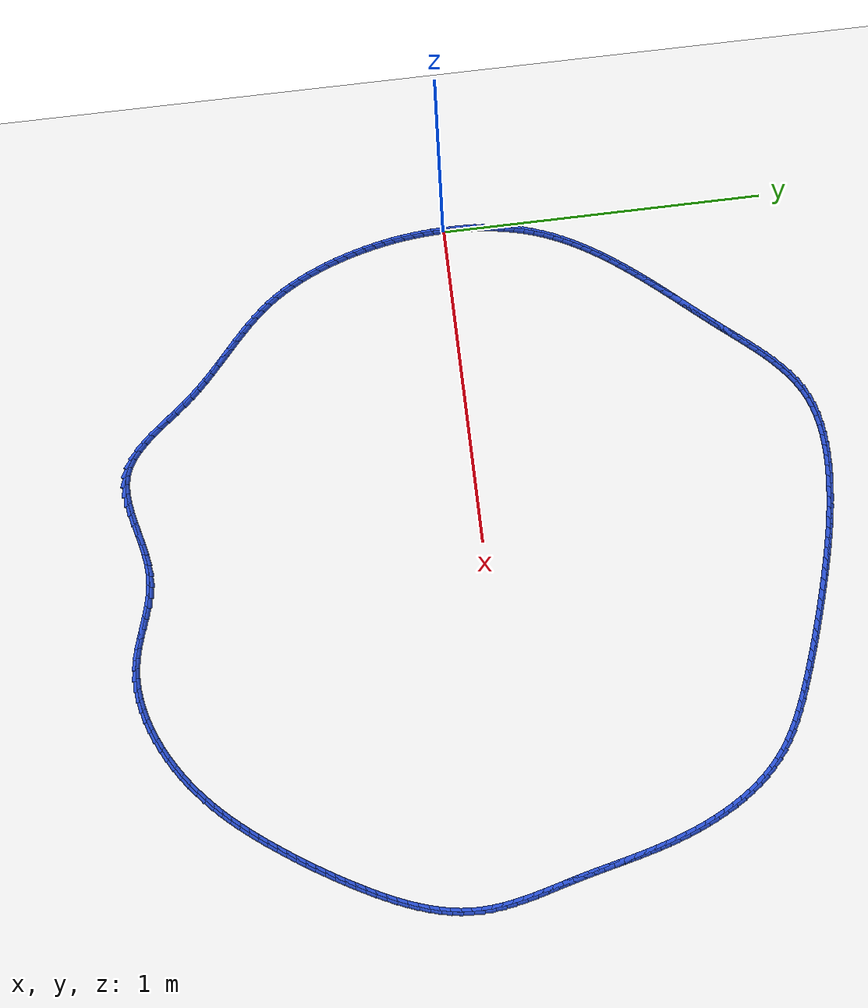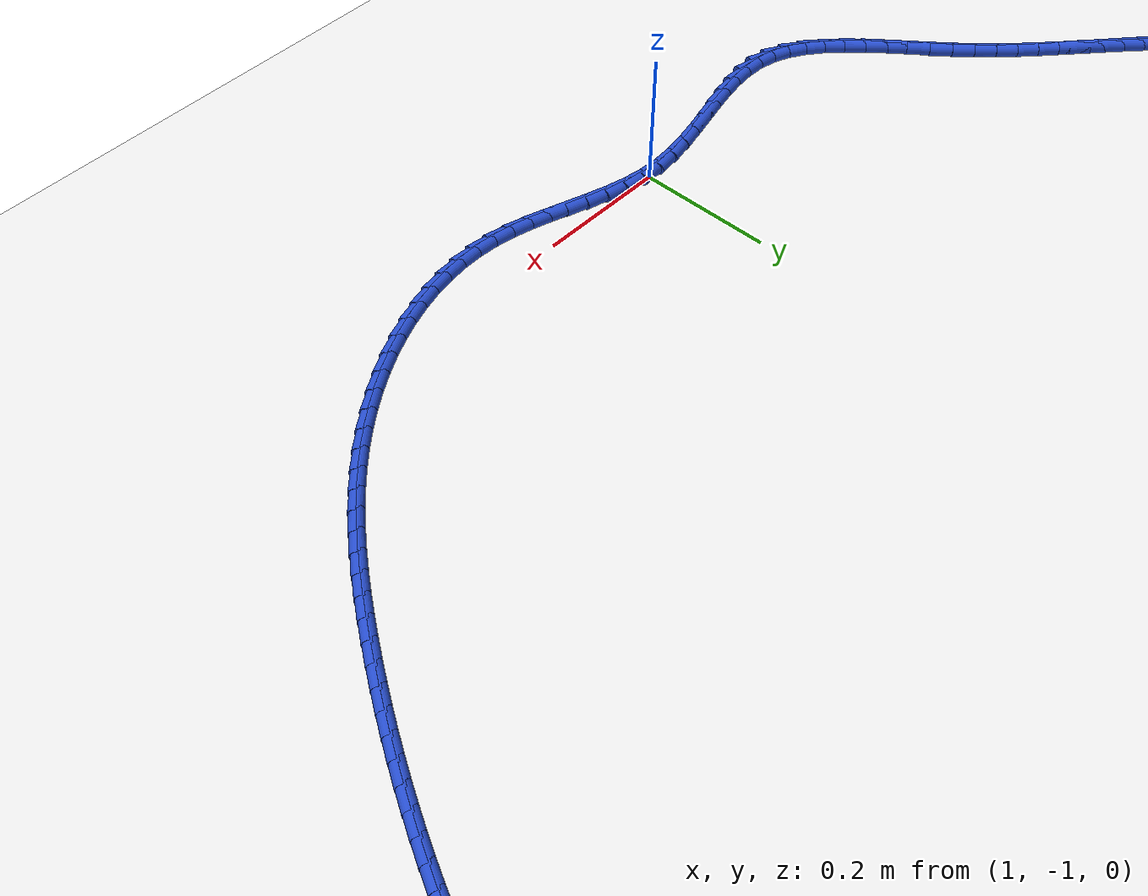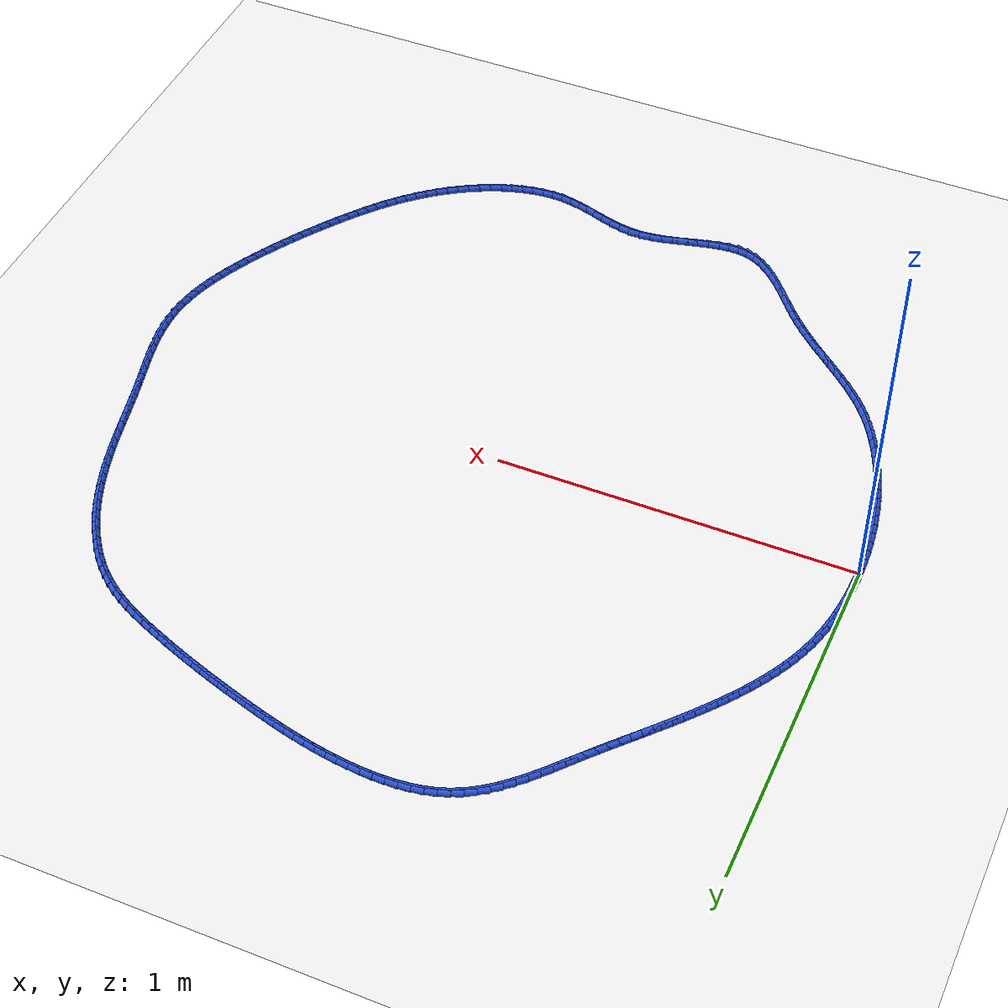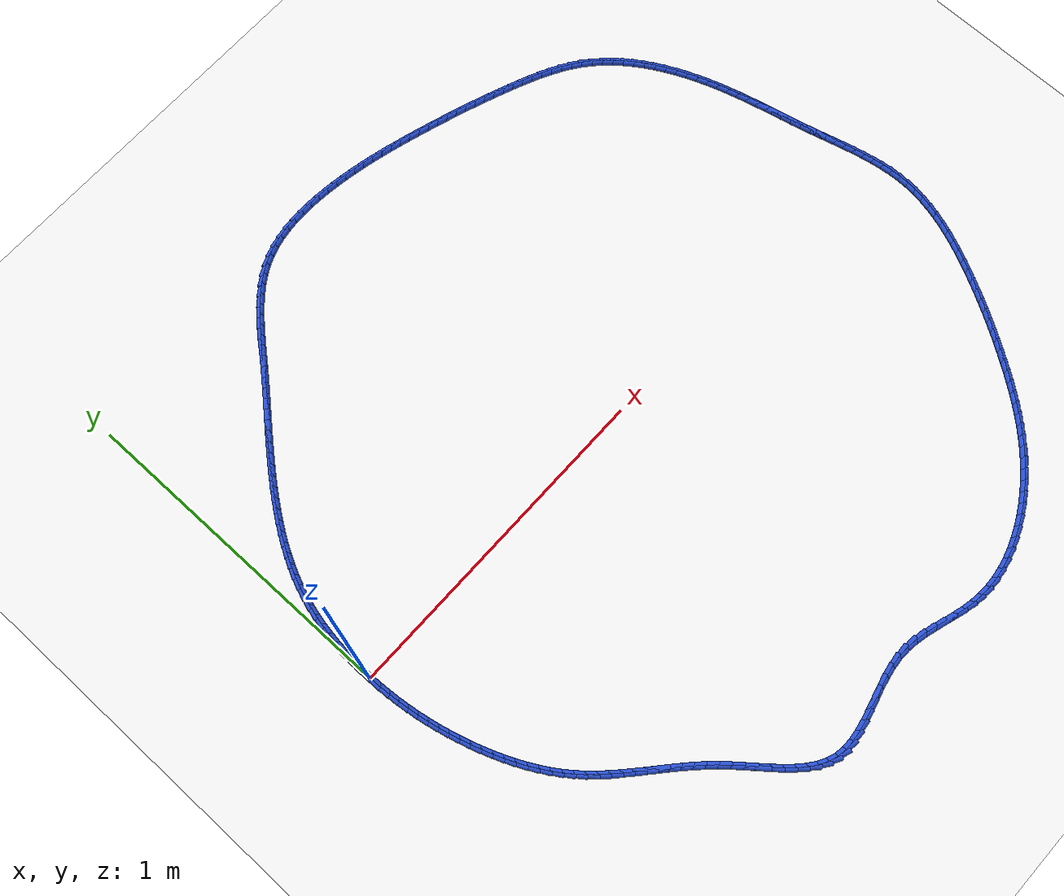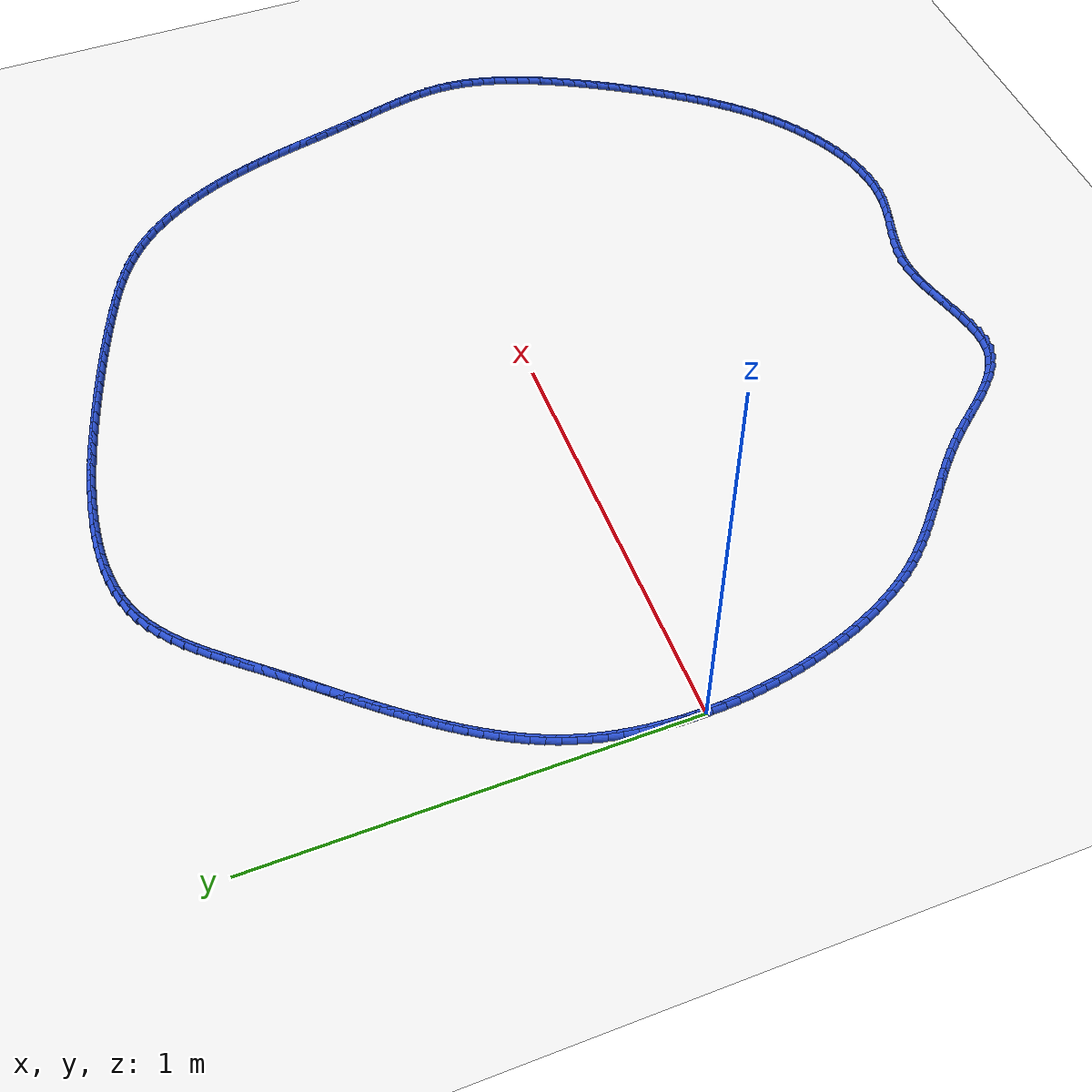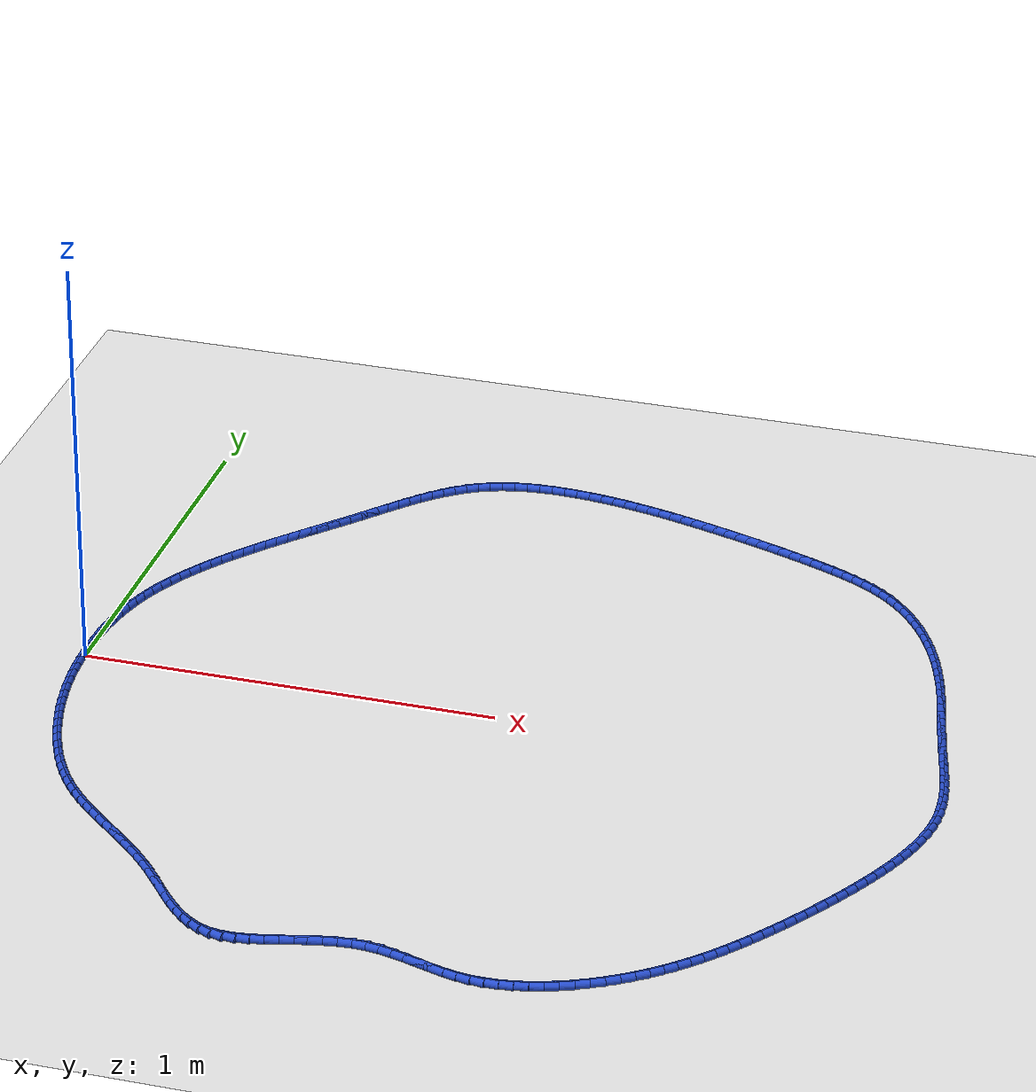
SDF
<sdf version="1.6">
 <world name="default">
  <light name="sun" type="directional">
   <pose>0 0 10 0 -0 0</pose>
   <diffuse>0.8 0.8 0.8 1</diffuse>
   <specular>0.2 0.2 0.2 1</specular>
   <attenuation>
    <range>1000</range>
    <constant>0.9</constant>
    <linear>0.01</linear>
    <quadratic>0.001</quadratic>
   </attenuation>
   <direction>-0.5 0.1 -0.9</direction>
  </light>
  <model name="ground_plane">
   <static>1</static>
   <link name="link">
    <collision name="collision">
     <geometry><plane><normal>0 0 1</normal><size>100 100</size></plane></geometry>
     <surface><friction><ode><mu>100</mu><mu2>50</mu2></ode></friction></surface>
    </collision>
    <visual name="visual">
     <cast_shadows>0</cast_shadows>
     <geometry><plane><normal>0 0 1</normal><size>100 100</size></plane></geometry>
     <material>
      <script><uri>file://media/materials/scripts/gazebo.material</uri><name>Gazebo/WhiteGlow</name></script>
     </material>
    </visual>
   </link>
  </model>
  <gravity>0 0 -9.8</gravity>
  <magnetic_field>6e-06 2.3e-05 -4.2e-05</magnetic_field>
  <atmosphere type="adiabatic"/>
  <physics name="default_physics" default="0" type="ode">
   <max_step_size>0.001</max_step_size>
   <real_time_factor>1</real_time_factor>
   <real_time_update_rate>1000</real_time_update_rate>
  </physics>
  <scene><ambient>0.4 0.4 0.4 1</ambient><background>0.7 0.7 0.7 1</background><shadows>1</shadows></scene>
  <spherical_coordinates>
   <surface_model>EARTH_WGS84</surface_model>
   <latitude_deg>0</latitude_deg>
   <longitude_deg>0</longitude_deg>
   <elevation>0</elevation>
   <heading_deg>0</heading_deg>
  </spherical_coordinates>
  <model name="line">
   <link name="link_0">
    <pose>-1.3877787807814457e-17 4.163336342344337e-17 0.01 0 1.57 1.5698443958158221</pose>
    <collision name="collision">
     <geometry><cylinder><radius>0.01</radius><length>0.08</length></cylinder></geometry>
    </collision>
    <visual name="visual">
     <material>
      <script><name>Gazebo/Blue</name><uri>file://media/materials/scripts/gazebo.material</uri></script>
     </material>
     <geometry><cylinder><radius>0.01</radius><length>0.08</length></cylinder></geometry>
    </visual>
   </link>
   <link name="link_1">
    <pose>3.0045780102942897e-05 0.03156297219848614 0.01 0 1.57 1.5397682604223815</pose>
    <collision name="collision">
     <geometry><cylinder><radius>0.01</radius><length>0.08</length></cylinder></geometry>
    </collision>
    <visual name="visual">
     <material>
      <script><name>Gazebo/Blue</name><uri>file://media/materials/scripts/gazebo.material</uri></script>
     </material>
     <geometry><cylinder><radius>0.01</radius><length>0.08</length></cylinder></geometry>
    </visual>
   </link>
   <link name="link_2">
    <pose>0.001010997331743516 0.06316780115989125 0.01 0 1.57 1.507912348329897</pose>
    <collision name="collision">
     <geometry><cylinder><radius>0.01</radius><length>0.08</length></cylinder></geometry>
    </collision>
    <visual name="visual">
     <material>
      <script><name>Gazebo/Blue</name><uri>file://media/materials/scripts/gazebo.material</uri></script>
     </material>
     <geometry><cylinder><radius>0.01</radius><length>0.08</length></cylinder></geometry>
    </visual>
   </link>
   <link name="link_3">
    <pose>0.0029993892303460893 0.09474611878069684 0.01 0 1.57 1.4741468849337982</pose>
    <collision name="collision">
     <geometry><cylinder><radius>0.01</radius><length>0.08</length></cylinder></geometry>
    </collision>
    <visual name="visual">
     <material>
      <script><name>Gazebo/Blue</name><uri>file://media/materials/scripts/gazebo.material</uri></script>
     </material>
     <geometry><cylinder><radius>0.01</radius><length>0.08</length></cylinder></geometry>
    </visual>
   </link>
   <link name="link_4">
    <pose>0.006051756051335043 0.1262295569573845 0.01 0 1.57 1.4383435848633104</pose>
    <collision name="collision">
     <geometry><cylinder><radius>0.01</radius><length>0.08</length></cylinder></geometry>
    </collision>
    <visual name="visual">
     <material>
      <script><name>Gazebo/Blue</name><uri>file://media/materials/scripts/gazebo.material</uri></script>
     </material>
     <geometry><cylinder><radius>0.01</radius><length>0.08</length></cylinder></geometry>
    </visual>
   </link>
   <link name="link_5">
    <pose>0.010224632370134767 0.15754974758643575 0.01 0 1.57 1.400379091942559</pose>
    <collision name="collision">
     <geometry><cylinder><radius>0.01</radius><length>0.08</length></cylinder></geometry>
    </collision>
    <visual name="visual">
     <material>
      <script><name>Gazebo/Blue</name><uri>file://media/materials/scripts/gazebo.material</uri></script>
     </material>
     <geometry><cylinder><radius>0.01</radius><length>0.08</length></cylinder></geometry>
    </visual>
   </link>
   <link name="link_6">
    <pose>0.01557455276216965 0.18863832256433222 0.01 0 1.57 1.3601395310939663</pose>
    <collision name="collision">
     <geometry><cylinder><radius>0.01</radius><length>0.08</length></cylinder></geometry>
    </collision>
    <visual name="visual">
     <material>
      <script><name>Gazebo/Blue</name><uri>file://media/materials/scripts/gazebo.material</uri></script>
     </material>
     <geometry><cylinder><radius>0.01</radius><length>0.08</length></cylinder></geometry>
    </visual>
   </link>
   <link name="link_7">
    <pose>0.02215805180286407 0.21942691378755544 0.01 0 1.57 1.3175262920855786</pose>
    <collision name="collision">
     <geometry><cylinder><radius>0.01</radius><length>0.08</length></cylinder></geometry>
    </collision>
    <visual name="visual">
     <material>
      <script><name>Gazebo/Blue</name><uri>file://media/materials/scripts/gazebo.material</uri></script>
     </material>
     <geometry><cylinder><radius>0.01</radius><length>0.08</length></cylinder></geometry>
    </visual>
   </link>
   <link name="link_8">
    <pose>0.030031664067642398 0.24984715315258688 0.01 0 1.57 1.2724630907307373</pose>
    <collision name="collision">
     <geometry><cylinder><radius>0.01</radius><length>0.08</length></cylinder></geometry>
    </collision>
    <visual name="visual">
     <material>
      <script><name>Gazebo/Blue</name><uri>file://media/materials/scripts/gazebo.material</uri></script>
     </material>
     <geometry><cylinder><radius>0.01</radius><length>0.08</length></cylinder></geometry>
    </visual>
   </link>
   <link name="link_9">
    <pose>0.039251924131929045 0.2798306725559082 0.01 0 1.57 1.2250217477937682</pose>
    <collision name="collision">
     <geometry><cylinder><radius>0.01</radius><length>0.08</length></cylinder></geometry>
    </collision>
    <visual name="visual">
     <material>
      <script><name>Gazebo/Blue</name><uri>file://media/materials/scripts/gazebo.material</uri></script>
     </material>
     <geometry><cylinder><radius>0.01</radius><length>0.08</length></cylinder></geometry>
    </visual>
   </link>
   <link name="link_10">
    <pose>0.049872050590693454 0.3093107644458877 0.01 0 1.57 1.17796529472601</pose>
    <collision name="collision">
     <geometry><cylinder><radius>0.01</radius><length>0.08</length></cylinder></geometry>
    </collision>
    <visual name="visual">
     <material>
      <script><name>Gazebo/Blue</name><uri>file://media/materials/scripts/gazebo.material</uri></script>
     </material>
     <geometry><cylinder><radius>0.01</radius><length>0.08</length></cylinder></geometry>
    </visual>
   </link>
   <link name="link_11">
    <pose>0.061867543199253985 0.33825964073003056 0.01 0 1.57 1.1341441911589485</pose>
    <collision name="collision">
     <geometry><cylinder><radius>0.01</radius><length>0.08</length></cylinder></geometry>
    </collision>
    <visual name="visual">
     <material>
      <script><name>Gazebo/Blue</name><uri>file://media/materials/scripts/gazebo.material</uri></script>
     </material>
     <geometry><cylinder><radius>0.01</radius><length>0.08</length></cylinder></geometry>
    </visual>
   </link>
   <link name="link_12">
    <pose>0.07513536794758885 0.36668884086736925 0.01 0 1.57 1.0937105369907951</pose>
    <collision name="collision">
     <geometry><cylinder><radius>0.01</radius><length>0.08</length></cylinder></geometry>
    </collision>
    <visual name="visual">
     <material>
      <script><name>Gazebo/Blue</name><uri>file://media/materials/scripts/gazebo.material</uri></script>
     </material>
     <geometry><cylinder><radius>0.01</radius><length>0.08</length></cylinder></geometry>
    </visual>
   </link>
   <link name="link_13">
    <pose>0.08956901185452446 0.39461164649008545 0.01 0 1.57 1.0566431709803492</pose>
    <collision name="collision">
     <geometry><cylinder><radius>0.01</radius><length>0.08</length></cylinder></geometry>
    </collision>
    <visual name="visual">
     <material>
      <script><name>Gazebo/Blue</name><uri>file://media/materials/scripts/gazebo.material</uri></script>
     </material>
     <geometry><cylinder><radius>0.01</radius><length>0.08</length></cylinder></geometry>
    </visual>
   </link>
   <link name="link_14">
    <pose>0.10506196193888712 0.42204133923036036 0.01 0 1.57 1.022885207896108</pose>
    <collision name="collision">
     <geometry><cylinder><radius>0.01</radius><length>0.08</length></cylinder></geometry>
    </collision>
    <visual name="visual">
     <material>
      <script><name>Gazebo/Blue</name><uri>file://media/materials/scripts/gazebo.material</uri></script>
     </material>
     <geometry><cylinder><radius>0.01</radius><length>0.08</length></cylinder></geometry>
    </visual>
   </link>
   <link name="link_15">
    <pose>0.12150770521950315 0.4489912007203753 0.01 0 1.57 0.9923568375646948</pose>
    <collision name="collision">
     <geometry><cylinder><radius>0.01</radius><length>0.08</length></cylinder></geometry>
    </collision>
    <visual name="visual">
     <material>
      <script><name>Gazebo/Blue</name><uri>file://media/materials/scripts/gazebo.material</uri></script>
     </material>
     <geometry><cylinder><radius>0.01</radius><length>0.08</length></cylinder></geometry>
    </visual>
   </link>
   <link name="link_16">
    <pose>0.13879972871519883 0.4754745125923115 0.01 0 1.57 0.9649662804064286</pose>
    <collision name="collision">
     <geometry><cylinder><radius>0.01</radius><length>0.08</length></cylinder></geometry>
    </collision>
    <visual name="visual">
     <material>
      <script><name>Gazebo/Blue</name><uri>file://media/materials/scripts/gazebo.material</uri></script>
     </material>
     <geometry><cylinder><radius>0.01</radius><length>0.08</length></cylinder></geometry>
    </visual>
   </link>
   <link name="link_17">
    <pose>0.15683151944480056 0.5015045564783505 0.01 0 1.57 0.9406188449625145</pose>
    <collision name="collision">
     <geometry><cylinder><radius>0.01</radius><length>0.08</length></cylinder></geometry>
    </collision>
    <visual name="visual">
     <material>
      <script><name>Gazebo/Blue</name><uri>file://media/materials/scripts/gazebo.material</uri></script>
     </material>
     <geometry><cylinder><radius>0.01</radius><length>0.08</length></cylinder></geometry>
    </visual>
   </link>
   <link name="link_18">
    <pose>0.17549656442713457 0.5270946140106734 0.01 0 1.57 0.9192242530750864</pose>
    <collision name="collision">
     <geometry><cylinder><radius>0.01</radius><length>0.08</length></cylinder></geometry>
    </collision>
    <visual name="visual">
     <material>
      <script><name>Gazebo/Blue</name><uri>file://media/materials/scripts/gazebo.material</uri></script>
     </material>
     <geometry><cylinder><radius>0.01</radius><length>0.08</length></cylinder></geometry>
    </visual>
   </link>
   <link name="link_19">
    <pose>0.19468835068102744 0.552257966821462 0.01 0 1.57 0.9007025164065035</pose>
    <collision name="collision">
     <geometry><cylinder><radius>0.01</radius><length>0.08</length></cylinder></geometry>
    </collision>
    <visual name="visual">
     <material>
      <script><name>Gazebo/Blue</name><uri>file://media/materials/scripts/gazebo.material</uri></script>
     </material>
     <geometry><cylinder><radius>0.01</radius><length>0.08</length></cylinder></geometry>
    </visual>
   </link>
   <link name="link_20">
    <pose>0.21430036522530516 0.5770078965428969 0.01 0 1.57 0.8849886950662461</pose>
    <collision name="collision">
     <geometry><cylinder><radius>0.01</radius><length>0.08</length></cylinder></geometry>
    </collision>
    <visual name="visual">
     <material>
      <script><name>Gazebo/Blue</name><uri>file://media/materials/scripts/gazebo.material</uri></script>
     </material>
     <geometry><cylinder><radius>0.01</radius><length>0.08</length></cylinder></geometry>
    </visual>
   </link>
   <link name="link_21">
    <pose>0.23422609507879427 0.60135768480716 0.01 0 1.57 0.8719955283070995</pose>
    <collision name="collision">
     <geometry><cylinder><radius>0.01</radius><length>0.08</length></cylinder></geometry>
    </collision>
    <visual name="visual">
     <material>
      <script><name>Gazebo/Blue</name><uri>file://media/materials/scripts/gazebo.material</uri></script>
     </material>
     <geometry><cylinder><radius>0.01</radius><length>0.08</length></cylinder></geometry>
    </visual>
   </link>
   <link name="link_22">
    <pose>0.25436846574544564 0.6253298348117089 0.01 0 1.57 0.8615007942577673</pose>
    <collision name="collision">
     <geometry><cylinder><radius>0.01</radius><length>0.08</length></cylinder></geometry>
    </collision>
    <visual name="visual">
     <material>
      <script><name>Gazebo/Blue</name><uri>file://media/materials/scripts/gazebo.material</uri></script>
     </material>
     <geometry><cylinder><radius>0.01</radius><length>0.08</length></cylinder></geometry>
    </visual>
   </link>
   <link name="link_23">
    <pose>0.27468400698269424 0.6489992220485035 0.01 0 1.57 0.8534972518807313</pose>
    <collision name="collision">
     <geometry><cylinder><radius>0.01</radius><length>0.08</length></cylinder></geometry>
    </collision>
    <visual name="visual">
     <material>
      <script><name>Gazebo/Blue</name><uri>file://media/materials/scripts/gazebo.material</uri></script>
     </material>
     <geometry><cylinder><radius>0.01</radius><length>0.08</length></cylinder></geometry>
    </visual>
   </link>
   <link name="link_24">
    <pose>0.29514814793866956 0.672459187045224 0.01 0 1.57 0.848042734042865</pose>
    <collision name="collision">
     <geometry><cylinder><radius>0.01</radius><length>0.08</length></cylinder></geometry>
    </collision>
    <visual name="visual">
     <material>
      <script><name>Gazebo/Blue</name><uri>file://media/materials/scripts/gazebo.material</uri></script>
     </material>
     <geometry><cylinder><radius>0.01</radius><length>0.08</length></cylinder></geometry>
    </visual>
   </link>
   <link name="link_25">
    <pose>0.3157363390555596 0.6958030911342187 0.01 0 1.57 0.8451673537912384</pose>
    <collision name="collision">
     <geometry><cylinder><radius>0.01</radius><length>0.08</length></cylinder></geometry>
    </collision>
    <visual name="visual">
     <material>
      <script><name>Gazebo/Blue</name><uri>file://media/materials/scripts/gazebo.material</uri></script>
     </material>
     <geometry><cylinder><radius>0.01</radius><length>0.08</length></cylinder></geometry>
    </visual>
   </link>
   <link name="link_26">
    <pose>0.3364240307755524 0.7191242956478366 0.01 0 1.57 0.8448739147285522</pose>
    <collision name="collision">
     <geometry><cylinder><radius>0.01</radius><length>0.08</length></cylinder></geometry>
    </collision>
    <visual name="visual">
     <material>
      <script><name>Gazebo/Blue</name><uri>file://media/materials/scripts/gazebo.material</uri></script>
     </material>
     <geometry><cylinder><radius>0.01</radius><length>0.08</length></cylinder></geometry>
    </visual>
   </link>
   <link name="link_27">
    <pose>0.35718667354083594 0.7425161619184262 0.01 0 1.57 0.8471386394500002</pose>
    <collision name="collision">
     <geometry><cylinder><radius>0.01</radius><length>0.08</length></cylinder></geometry>
    </collision>
    <visual name="visual">
     <material>
      <script><name>Gazebo/Blue</name><uri>file://media/materials/scripts/gazebo.material</uri></script>
     </material>
     <geometry><cylinder><radius>0.01</radius><length>0.08</length></cylinder></geometry>
    </visual>
   </link>
   <link name="link_28">
    <pose>0.3779997177935982 0.7660720512783356 0.01 0 1.57 0.8519120639241413</pose>
    <collision name="collision">
     <geometry><cylinder><radius>0.01</radius><length>0.08</length></cylinder></geometry>
    </collision>
    <visual name="visual">
     <material>
      <script><name>Gazebo/Blue</name><uri>file://media/materials/scripts/gazebo.material</uri></script>
     </material>
     <geometry><cylinder><radius>0.01</radius><length>0.08</length></cylinder></geometry>
    </visual>
   </link>
   <link name="link_29">
    <pose>0.39883861397602693 0.7898853250599132 0.01 0 1.57 0.859120080386922</pose>
    <collision name="collision">
     <geometry><cylinder><radius>0.01</radius><length>0.08</length></cylinder></geometry>
    </collision>
    <visual name="visual">
     <material>
      <script><name>Gazebo/Blue</name><uri>file://media/materials/scripts/gazebo.material</uri></script>
     </material>
     <geometry><cylinder><radius>0.01</radius><length>0.08</length></cylinder></geometry>
    </visual>
   </link>
   <link name="link_30">
    <pose>0.4196788125303105 0.8140493445955079 0.01 0 1.57 0.8673544095922836</pose>
    <collision name="collision">
     <geometry><cylinder><radius>0.01</radius><length>0.08</length></cylinder></geometry>
    </collision>
    <visual name="visual">
     <material>
      <script><name>Gazebo/Blue</name><uri>file://media/materials/scripts/gazebo.material</uri></script>
     </material>
     <geometry><cylinder><radius>0.01</radius><length>0.08</length></cylinder></geometry>
    </visual>
   </link>
   <link name="link_31">
    <pose>0.44051322497126755 0.8386127440083433 0.01 0 1.57 0.8689951062572088</pose>
    <collision name="collision">
     <geometry><cylinder><radius>0.01</radius><length>0.08</length></cylinder></geometry>
    </collision>
    <visual name="visual">
     <material>
      <script><name>Gazebo/Blue</name><uri>file://media/materials/scripts/gazebo.material</uri></script>
     </material>
     <geometry><cylinder><radius>0.01</radius><length>0.08</length></cylinder></geometry>
    </visual>
   </link>
   <link name="link_32">
    <pose>0.461436617008372 0.8633632539845622 0.01 0 1.57 0.8614293373775493</pose>
    <collision name="collision">
     <geometry><cylinder><radius>0.01</radius><length>0.08</length></cylinder></geometry>
    </collision>
    <visual name="visual">
     <material>
      <script><name>Gazebo/Blue</name><uri>file://media/materials/scripts/gazebo.material</uri></script>
     </material>
     <geometry><cylinder><radius>0.01</radius><length>0.08</length></cylinder></geometry>
    </visual>
   </link>
   <link name="link_33">
    <pose>0.4825805829990302 0.887994267212138 0.01 0 1.57 0.8445967064743418</pose>
    <collision name="collision">
     <geometry><cylinder><radius>0.01</radius><length>0.08</length></cylinder></geometry>
    </collision>
    <visual name="visual">
     <material>
      <script><name>Gazebo/Blue</name><uri>file://media/materials/scripts/gazebo.material</uri></script>
     </material>
     <geometry><cylinder><radius>0.01</radius><length>0.08</length></cylinder></geometry>
    </visual>
   </link>
   <link name="link_34">
    <pose>0.5040767677097081 0.9121990472543016 0.01 0 1.57 0.8182070951453911</pose>
    <collision name="collision">
     <geometry><cylinder><radius>0.01</radius><length>0.08</length></cylinder></geometry>
    </collision>
    <visual name="visual">
     <material>
      <script><name>Gazebo/Blue</name><uri>file://media/materials/scripts/gazebo.material</uri></script>
     </material>
     <geometry><cylinder><radius>0.01</radius><length>0.08</length></cylinder></geometry>
    </visual>
   </link>
   <link name="link_35">
    <pose>0.5260568159068716 0.9356708576742824 0.01 0 1.57 0.7817681420238595</pose>
    <collision name="collision">
     <geometry><cylinder><radius>0.01</radius><length>0.08</length></cylinder></geometry>
    </collision>
    <visual name="visual">
     <material>
      <script><name>Gazebo/Blue</name><uri>file://media/materials/scripts/gazebo.material</uri></script>
     </material>
     <geometry><cylinder><radius>0.01</radius><length>0.08</length></cylinder></geometry>
    </visual>
   </link>
   <link name="link_36">
    <pose>0.5486523723569867 0.9581029620353106 0.01 0 1.57 0.7346398563368759</pose>
    <collision name="collision">
     <geometry><cylinder><radius>0.01</radius><length>0.08</length></cylinder></geometry>
    </collision>
    <visual name="visual">
     <material>
      <script><name>Gazebo/Blue</name><uri>file://media/materials/scripts/gazebo.material</uri></script>
     </material>
     <geometry><cylinder><radius>0.01</radius><length>0.08</length></cylinder></geometry>
    </visual>
   </link>
   <link name="link_37">
    <pose>0.5719950818265193 0.979188623900616 0.01 0 1.57 0.6761309491833303</pose>
    <collision name="collision">
     <geometry><cylinder><radius>0.01</radius><length>0.08</length></cylinder></geometry>
    </collision>
    <visual name="visual">
     <material>
      <script><name>Gazebo/Blue</name><uri>file://media/materials/scripts/gazebo.material</uri></script>
     </material>
     <geometry><cylinder><radius>0.01</radius><length>0.08</length></cylinder></geometry>
    </visual>
   </link>
   <link name="link_38">
    <pose>0.5962165890819353 0.9986211068334288 0.01 0 1.57 0.6056597134405197</pose>
    <collision name="collision">
     <geometry><cylinder><radius>0.01</radius><length>0.08</length></cylinder></geometry>
    </collision>
    <visual name="visual">
     <material>
      <script><name>Gazebo/Blue</name><uri>file://media/materials/scripts/gazebo.material</uri></script>
     </material>
     <geometry><cylinder><radius>0.01</radius><length>0.08</length></cylinder></geometry>
    </visual>
   </link>
   <link name="link_39">
    <pose>0.6214485388897006 1.0160936743969784 0.01 0 1.57 0.5229973598351159</pose>
    <collision name="collision">
     <geometry><cylinder><radius>0.01</radius><length>0.08</length></cylinder></geometry>
    </collision>
    <visual name="visual">
     <material>
      <script><name>Gazebo/Blue</name><uri>file://media/materials/scripts/gazebo.material</uri></script>
     </material>
     <geometry><cylinder><radius>0.01</radius><length>0.08</length></cylinder></geometry>
    </visual>
   </link>
   <link name="link_40">
    <pose>0.6478225760162815 1.0312995901544952 0.01 0 1.57 0.42885585457572645</pose>
    <collision name="collision">
     <geometry><cylinder><radius>0.01</radius><length>0.08</length></cylinder></geometry>
    </collision>
    <visual name="visual">
     <material>
      <script><name>Gazebo/Blue</name><uri>file://media/materials/scripts/gazebo.material</uri></script>
     </material>
     <geometry><cylinder><radius>0.01</radius><length>0.08</length></cylinder></geometry>
    </visual>
   </link>
   <link name="link_41">
    <pose>0.6754659308966621 1.0439391534803533 0.01 0 1.57 0.3330858787879804</pose>
    <collision name="collision">
     <geometry><cylinder><radius>0.01</radius><length>0.08</length></cylinder></geometry>
    </collision>
    <visual name="visual">
     <material>
      <script><name>Gazebo/Blue</name><uri>file://media/materials/scripts/gazebo.material</uri></script>
     </material>
     <geometry><cylinder><radius>0.01</radius><length>0.08</length></cylinder></geometry>
    </visual>
   </link>
   <link name="link_42">
    <pose>0.7043647845391011 1.053937476301539 0.01 0 1.57 0.2467208546980149</pose>
    <collision name="collision">
     <geometry><cylinder><radius>0.01</radius><length>0.08</length></cylinder></geometry>
    </collision>
    <visual name="visual">
     <material>
      <script><name>Gazebo/Blue</name><uri>file://media/materials/scripts/gazebo.material</uri></script>
     </material>
     <geometry><cylinder><radius>0.01</radius><length>0.08</length></cylinder></geometry>
    </visual>
   </link>
   <link name="link_43">
    <pose>0.7343380347744847 1.0614862959329474 0.01 0 1.57 0.17030666743963532</pose>
    <collision name="collision">
     <geometry><cylinder><radius>0.01</radius><length>0.08</length></cylinder></geometry>
    </collision>
    <visual name="visual">
     <material>
      <script><name>Gazebo/Blue</name><uri>file://media/materials/scripts/gazebo.material</uri></script>
     </material>
     <geometry><cylinder><radius>0.01</radius><length>0.08</length></cylinder></geometry>
    </visual>
   </link>
   <link name="link_44">
    <pose>0.7651948704491341 1.0667928244181089 0.01 0 1.57 0.10332297264583283</pose>
    <collision name="collision">
     <geometry><cylinder><radius>0.01</radius><length>0.08</length></cylinder></geometry>
    </collision>
    <visual name="visual">
     <material>
      <script><name>Gazebo/Blue</name><uri>file://media/materials/scripts/gazebo.material</uri></script>
     </material>
     <geometry><cylinder><radius>0.01</radius><length>0.08</length></cylinder></geometry>
    </visual>
   </link>
   <link name="link_45">
    <pose>0.7967444804093707 1.0700642738005548 0.01 0 1.57 0.04500894174793558</pose>
    <collision name="collision">
     <geometry><cylinder><radius>0.01</radius><length>0.08</length></cylinder></geometry>
    </collision>
    <visual name="visual">
     <material>
      <script><name>Gazebo/Blue</name><uri>file://media/materials/scripts/gazebo.material</uri></script>
     </material>
     <geometry><cylinder><radius>0.01</radius><length>0.08</length></cylinder></geometry>
    </visual>
   </link>
   <link name="link_46">
    <pose>0.828796053501517 1.0715078561238165 0.01 0 1.57 -0.005471446703290838</pose>
    <collision name="collision">
     <geometry><cylinder><radius>0.01</radius><length>0.08</length></cylinder></geometry>
    </collision>
    <visual name="visual">
     <material>
      <script><name>Gazebo/Blue</name><uri>file://media/materials/scripts/gazebo.material</uri></script>
     </material>
     <geometry><cylinder><radius>0.01</radius><length>0.08</length></cylinder></geometry>
    </visual>
   </link>
   <link name="link_47">
    <pose>0.8611587785718946 1.0713307834314247 0.01 0 1.57 -0.04892538156265053</pose>
    <collision name="collision">
     <geometry><cylinder><radius>0.01</radius><length>0.08</length></cylinder></geometry>
    </collision>
    <visual name="visual">
     <material>
      <script><name>Gazebo/Blue</name><uri>file://media/materials/scripts/gazebo.material</uri></script>
     </material>
     <geometry><cylinder><radius>0.01</radius><length>0.08</length></cylinder></geometry>
    </visual>
   </link>
   <link name="link_48">
    <pose>0.893641844466825 1.0697402677669101 0.01 0 1.57 -0.08607260760630311</pose>
    <collision name="collision">
     <geometry><cylinder><radius>0.01</radius><length>0.08</length></cylinder></geometry>
    </collision>
    <visual name="visual">
     <material>
      <script><name>Gazebo/Blue</name><uri>file://media/materials/scripts/gazebo.material</uri></script>
     </material>
     <geometry><cylinder><radius>0.01</radius><length>0.08</length></cylinder></geometry>
    </visual>
   </link>
   <link name="link_49">
    <pose>0.9260544400326303 1.0669435211738039 0.01 0 1.57 -0.1175158398029808</pose>
    <collision name="collision">
     <geometry><cylinder><radius>0.01</radius><length>0.08</length></cylinder></geometry>
    </collision>
    <visual name="visual">
     <material>
      <script><name>Gazebo/Blue</name><uri>file://media/materials/scripts/gazebo.material</uri></script>
     </material>
     <geometry><cylinder><radius>0.01</radius><length>0.08</length></cylinder></geometry>
    </visual>
   </link>
   <link name="link_50">
    <pose>0.9582057790823607 1.063147740246219 0.01 0 1.57 -0.14445269814854006</pose>
    <collision name="collision">
     <geometry><cylinder><radius>0.01</radius><length>0.08</length></cylinder></geometry>
    </collision>
    <visual name="visual">
     <material>
      <script><name>Gazebo/Blue</name><uri>file://media/materials/scripts/gazebo.material</uri></script>
     </material>
     <geometry><cylinder><radius>0.01</radius><length>0.08</length></cylinder></geometry>
    </visual>
   </link>
   <link name="link_51">
    <pose>0.9899548246608469 1.0585293367408706 0.01 0 1.57 -0.16927994644267996</pose>
    <collision name="collision">
     <geometry><cylinder><radius>0.01</radius><length>0.08</length></cylinder></geometry>
    </collision>
    <visual name="visual">
     <material>
      <script><name>Gazebo/Blue</name><uri>file://media/materials/scripts/gazebo.material</uri></script>
     </material>
     <geometry><cylinder><radius>0.01</radius><length>0.08</length></cylinder></geometry>
    </visual>
   </link>
   <link name="link_52">
    <pose>1.0213144422700509 1.0531694875344833 0.01 0 1.57 -0.1923035712022563</pose>
    <collision name="collision">
     <geometry><cylinder><radius>0.01</radius><length>0.08</length></cylinder></geometry>
    </collision>
    <visual name="visual">
     <material>
      <script><name>Gazebo/Blue</name><uri>file://media/materials/scripts/gazebo.material</uri></script>
     </material>
     <geometry><cylinder><radius>0.01</radius><length>0.08</length></cylinder></geometry>
    </visual>
   </link>
   <link name="link_53">
    <pose>1.0523271668456238 1.0471310100506004 0.01 0 1.57 -0.21339380330619792</pose>
    <collision name="collision">
     <geometry><cylinder><radius>0.01</radius><length>0.08</length></cylinder></geometry>
    </collision>
    <visual name="visual">
     <material>
      <script><name>Gazebo/Blue</name><uri>file://media/materials/scripts/gazebo.material</uri></script>
     </material>
     <geometry><cylinder><radius>0.01</radius><length>0.08</length></cylinder></geometry>
    </visual>
   </link>
   <link name="link_54">
    <pose>1.083035533323215 1.040476721712764 0.01 0 1.57 -0.23244057360587123</pose>
    <collision name="collision">
     <geometry><cylinder><radius>0.01</radius><length>0.08</length></cylinder></geometry>
    </collision>
    <visual name="visual">
     <material>
      <script><name>Gazebo/Blue</name><uri>file://media/materials/scripts/gazebo.material</uri></script>
     </material>
     <geometry><cylinder><radius>0.01</radius><length>0.08</length></cylinder></geometry>
    </visual>
   </link>
   <link name="link_55">
    <pose>1.1134820766384745 1.033269439944516 0.01 0 1.57 -0.24935303393420907</pose>
    <collision name="collision">
     <geometry><cylinder><radius>0.01</radius><length>0.08</length></cylinder></geometry>
    </collision>
    <visual name="visual">
     <material>
      <script><name>Gazebo/Blue</name><uri>file://media/materials/scripts/gazebo.material</uri></script>
     </material>
     <geometry><cylinder><radius>0.01</radius><length>0.08</length></cylinder></geometry>
    </visual>
   </link>
   <link name="link_56">
    <pose>1.1437093317270541 1.0255719821693987 0.01 0 1.57 -0.26405859052661673</pose>
    <collision name="collision">
     <geometry><cylinder><radius>0.01</radius><length>0.08</length></cylinder></geometry>
    </collision>
    <visual name="visual">
     <material>
      <script><name>Gazebo/Blue</name><uri>file://media/materials/scripts/gazebo.material</uri></script>
     </material>
     <geometry><cylinder><radius>0.01</radius><length>0.08</length></cylinder></geometry>
    </visual>
   </link>
   <link name="link_57">
    <pose>1.1737598335246027 1.0174471658109545 0.01 0 1.57 -0.276501615960312</pose>
    <collision name="collision">
     <geometry><cylinder><radius>0.01</radius><length>0.08</length></cylinder></geometry>
    </collision>
    <visual name="visual">
     <material>
      <script><name>Gazebo/Blue</name><uri>file://media/materials/scripts/gazebo.material</uri></script>
     </material>
     <geometry><cylinder><radius>0.01</radius><length>0.08</length></cylinder></geometry>
    </visual>
   </link>
   <link name="link_58">
    <pose>1.2036761169667716 1.0089578082927264 0.01 0 1.57 -0.2866419984555087</pose>
    <collision name="collision">
     <geometry><cylinder><radius>0.01</radius><length>0.08</length></cylinder></geometry>
    </collision>
    <visual name="visual">
     <material>
      <script><name>Gazebo/Blue</name><uri>file://media/materials/scripts/gazebo.material</uri></script>
     </material>
     <geometry><cylinder><radius>0.01</radius><length>0.08</length></cylinder></geometry>
    </visual>
   </link>
   <link name="link_59">
    <pose>1.2335007169892103 1.0001667270382562 0.01 0 1.57 -0.29448605851409426</pose>
    <collision name="collision">
     <geometry><cylinder><radius>0.01</radius><length>0.08</length></cylinder></geometry>
    </collision>
    <visual name="visual">
     <material>
      <script><name>Gazebo/Blue</name><uri>file://media/materials/scripts/gazebo.material</uri></script>
     </material>
     <geometry><cylinder><radius>0.01</radius><length>0.08</length></cylinder></geometry>
    </visual>
   </link>
   <link name="link_60">
    <pose>1.2632756770650722 0.9911358354121959 0.01 0 1.57 -0.3012501766972722</pose>
    <collision name="collision">
     <geometry><cylinder><radius>0.01</radius><length>0.08</length></cylinder></geometry>
    </collision>
    <visual name="visual">
     <material>
      <script><name>Gazebo/Blue</name><uri>file://media/materials/scripts/gazebo.material</uri></script>
     </material>
     <geometry><cylinder><radius>0.01</radius><length>0.08</length></cylinder></geometry>
    </visual>
   </link>
   <link name="link_61">
    <pose>1.2930243788608966 0.9818927178685601 0.01 0 1.57 -0.30850913029278665</pose>
    <collision name="collision">
     <geometry><cylinder><radius>0.01</radius><length>0.08</length></cylinder></geometry>
    </collision>
    <visual name="visual">
     <material>
      <script><name>Gazebo/Blue</name><uri>file://media/materials/scripts/gazebo.material</uri></script>
     </material>
     <geometry><cylinder><radius>0.01</radius><length>0.08</length></cylinder></geometry>
    </visual>
   </link>
   <link name="link_62">
    <pose>1.322746215360632 0.9724208310146791 0.01 0 1.57 -0.31636105314010665</pose>
    <collision name="collision">
     <geometry><cylinder><radius>0.01</radius><length>0.08</length></cylinder></geometry>
    </collision>
    <visual name="visual">
     <material>
      <script><name>Gazebo/Blue</name><uri>file://media/materials/scripts/gazebo.material</uri></script>
     </material>
     <geometry><cylinder><radius>0.01</radius><length>0.08</length></cylinder></geometry>
    </visual>
   </link>
   <link name="link_63">
    <pose>1.3524390016083863 0.9627007287937996 0.01 0 1.57 -0.3247992721002125</pose>
    <collision name="collision">
     <geometry><cylinder><radius>0.01</radius><length>0.08</length></cylinder></geometry>
    </collision>
    <visual name="visual">
     <material>
      <script><name>Gazebo/Blue</name><uri>file://media/materials/scripts/gazebo.material</uri></script>
     </material>
     <geometry><cylinder><radius>0.01</radius><length>0.08</length></cylinder></geometry>
    </visual>
   </link>
   <link name="link_64">
    <pose>1.382100552648266 0.9527129651491686 0.01 0 1.57 -0.33381623935468535</pose>
    <collision name="collision">
     <geometry><cylinder><radius>0.01</radius><length>0.08</length></cylinder></geometry>
    </collision>
    <visual name="visual">
     <material>
      <script><name>Gazebo/Blue</name><uri>file://media/materials/scripts/gazebo.material</uri></script>
     </material>
     <geometry><cylinder><radius>0.01</radius><length>0.08</length></cylinder></geometry>
    </visual>
   </link>
   <link name="link_65">
    <pose>1.411728683524379 0.9424380940240334 0.01 0 1.57 -0.34340346854569054</pose>
    <collision name="collision">
     <geometry><cylinder><radius>0.01</radius><length>0.08</length></cylinder></geometry>
    </collision>
    <visual name="visual">
     <material>
      <script><name>Gazebo/Blue</name><uri>file://media/materials/scripts/gazebo.material</uri></script>
     </material>
     <geometry><cylinder><radius>0.01</radius><length>0.08</length></cylinder></geometry>
    </visual>
   </link>
   <link name="link_66">
    <pose>1.441321209280834 0.931856669361641 0.01 0 1.57 -0.3535514719870915</pose>
    <collision name="collision">
     <geometry><cylinder><radius>0.01</radius><length>0.08</length></cylinder></geometry>
    </collision>
    <visual name="visual">
     <material>
      <script><name>Gazebo/Blue</name><uri>file://media/materials/scripts/gazebo.material</uri></script>
     </material>
     <geometry><cylinder><radius>0.01</radius><length>0.08</length></cylinder></geometry>
    </visual>
   </link>
   <link name="link_67">
    <pose>1.4708759449617368 0.920949245105238 0.01 0 1.57 -0.3642497002878182</pose>
    <collision name="collision">
     <geometry><cylinder><radius>0.01</radius><length>0.08</length></cylinder></geometry>
    </collision>
    <visual name="visual">
     <material>
      <script><name>Gazebo/Blue</name><uri>file://media/materials/scripts/gazebo.material</uri></script>
     </material>
     <geometry><cylinder><radius>0.01</radius><length>0.08</length></cylinder></geometry>
    </visual>
   </link>
   <link name="link_68">
    <pose>1.5003907056111956 0.9096963751980718 0.01 0 1.57 -0.3754864858232488</pose>
    <collision name="collision">
     <geometry><cylinder><radius>0.01</radius><length>0.08</length></cylinder></geometry>
    </collision>
    <visual name="visual">
     <material>
      <script><name>Gazebo/Blue</name><uri>file://media/materials/scripts/gazebo.material</uri></script>
     </material>
     <geometry><cylinder><radius>0.01</radius><length>0.08</length></cylinder></geometry>
    </visual>
   </link>
   <link name="link_69">
    <pose>1.5298633062733182 0.8980786135833891 0.01 0 1.57 -0.3882064209361617</pose>
    <collision name="collision">
     <geometry><cylinder><radius>0.01</radius><length>0.08</length></cylinder></geometry>
    </collision>
    <visual name="visual">
     <material>
      <script><name>Gazebo/Blue</name><uri>file://media/materials/scripts/gazebo.material</uri></script>
     </material>
     <geometry><cylinder><radius>0.01</radius><length>0.08</length></cylinder></geometry>
    </visual>
   </link>
   <link name="link_70">
    <pose>1.55926610156848 0.8860540515846597 0.01 0 1.57 -0.40705466047487626</pose>
    <collision name="collision">
     <geometry><cylinder><radius>0.01</radius><length>0.08</length></cylinder></geometry>
    </collision>
    <visual name="visual">
     <material>
      <script><name>Gazebo/Blue</name><uri>file://media/materials/scripts/gazebo.material</uri></script>
     </material>
     <geometry><cylinder><radius>0.01</radius><length>0.08</length></cylinder></geometry>
    </visual>
   </link>
   <link name="link_71">
    <pose>1.5884486663612982 0.8734724573097219 0.01 0 1.57 -0.43357389648596206</pose>
    <collision name="collision">
     <geometry><cylinder><radius>0.01</radius><length>0.08</length></cylinder></geometry>
    </collision>
    <visual name="visual">
     <material>
      <script><name>Gazebo/Blue</name><uri>file://media/materials/scripts/gazebo.material</uri></script>
     </material>
     <geometry><cylinder><radius>0.01</radius><length>0.08</length></cylinder></geometry>
    </visual>
   </link>
   <link name="link_72">
    <pose>1.617223612572961 0.8601509880759243 0.01 0 1.57 -0.4680163771352982</pose>
    <collision name="collision">
     <geometry><cylinder><radius>0.01</radius><length>0.08</length></cylinder></geometry>
    </collision>
    <visual name="visual">
     <material>
      <script><name>Gazebo/Blue</name><uri>file://media/materials/scripts/gazebo.material</uri></script>
     </material>
     <geometry><cylinder><radius>0.01</radius><length>0.08</length></cylinder></geometry>
    </visual>
   </link>
   <link name="link_73">
    <pose>1.6454035447017041 0.8459067946516672 0.01 0 1.57 -0.5106870867776923</pose>
    <collision name="collision">
     <geometry><cylinder><radius>0.01</radius><length>0.08</length></cylinder></geometry>
    </collision>
    <visual name="visual">
     <material>
      <script><name>Gazebo/Blue</name><uri>file://media/materials/scripts/gazebo.material</uri></script>
     </material>
     <geometry><cylinder><radius>0.01</radius><length>0.08</length></cylinder></geometry>
    </visual>
   </link>
   <link name="link_74">
    <pose>1.67280106724576 0.8305570278053512 0.01 0 1.57 -0.5618813370693775</pose>
    <collision name="collision">
     <geometry><cylinder><radius>0.01</radius><length>0.08</length></cylinder></geometry>
    </collision>
    <visual name="visual">
     <material>
      <script><name>Gazebo/Blue</name><uri>file://media/materials/scripts/gazebo.material</uri></script>
     </material>
     <geometry><cylinder><radius>0.01</radius><length>0.08</length></cylinder></geometry>
    </visual>
   </link>
   <link name="link_75">
    <pose>1.6992287847033645 0.8139188383053765 0.01 0 1.57 -0.6217961640757254</pose>
    <collision name="collision">
     <geometry><cylinder><radius>0.01</radius><length>0.08</length></cylinder></geometry>
    </collision>
    <visual name="visual">
     <material>
      <script><name>Gazebo/Blue</name><uri>file://media/materials/scripts/gazebo.material</uri></script>
     </material>
     <geometry><cylinder><radius>0.01</radius><length>0.08</length></cylinder></geometry>
    </visual>
   </link>
   <link name="link_76">
    <pose>1.7244993015727503 0.7958093769201431 0.01 0 1.57 -0.689901114932038</pose>
    <collision name="collision">
     <geometry><cylinder><radius>0.01</radius><length>0.08</length></cylinder></geometry>
    </collision>
    <visual name="visual">
     <material>
      <script><name>Gazebo/Blue</name><uri>file://media/materials/scripts/gazebo.material</uri></script>
     </material>
     <geometry><cylinder><radius>0.01</radius><length>0.08</length></cylinder></geometry>
    </visual>
   </link>
   <link name="link_77">
    <pose>1.7484345565803976 0.7760587255309868 0.01 0 1.57 -0.7589189441751257</pose>
    <collision name="collision">
     <geometry><cylinder><radius>0.01</radius><length>0.08</length></cylinder></geometry>
    </collision>
    <visual name="visual">
     <material>
      <script><name>Gazebo/Blue</name><uri>file://media/materials/scripts/gazebo.material</uri></script>
     </material>
     <geometry><cylinder><radius>0.01</radius><length>0.08</length></cylinder></geometry>
    </visual>
   </link>
   <link name="link_78">
    <pose>1.7709837050751531 0.7546732047470565 0.01 0 1.57 -0.8235414793544874</pose>
    <collision name="collision">
     <geometry><cylinder><radius>0.01</radius><length>0.08</length></cylinder></geometry>
    </collision>
    <visual name="visual">
     <material>
      <script><name>Gazebo/Blue</name><uri>file://media/materials/scripts/gazebo.material</uri></script>
     </material>
     <geometry><cylinder><radius>0.01</radius><length>0.08</length></cylinder></geometry>
    </visual>
   </link>
   <link name="link_79">
    <pose>1.792187832656284 0.731786490157381 0.01 0 1.57 -0.8835822279837892</pose>
    <collision name="collision">
     <geometry><cylinder><radius>0.01</radius><length>0.08</length></cylinder></geometry>
    </collision>
    <visual name="visual">
     <material>
      <script><name>Gazebo/Blue</name><uri>file://media/materials/scripts/gazebo.material</uri></script>
     </material>
     <geometry><cylinder><radius>0.01</radius><length>0.08</length></cylinder></geometry>
    </visual>
   </link>
   <link name="link_80">
    <pose>1.8120900675731506 0.7075350871231285 0.01 0 1.57 -0.939108992367259</pose>
    <collision name="collision">
     <geometry><cylinder><radius>0.01</radius><length>0.08</length></cylinder></geometry>
    </collision>
    <visual name="visual">
     <material>
      <script><name>Gazebo/Blue</name><uri>file://media/materials/scripts/gazebo.material</uri></script>
     </material>
     <geometry><cylinder><radius>0.01</radius><length>0.08</length></cylinder></geometry>
    </visual>
   </link>
   <link name="link_81">
    <pose>1.8307335380751135 0.6820555010054672 0.01 0 1.57 -0.9902914331271295</pose>
    <collision name="collision">
     <geometry><cylinder><radius>0.01</radius><length>0.08</length></cylinder></geometry>
    </collision>
    <visual name="visual">
     <material>
      <script><name>Gazebo/Blue</name><uri>file://media/materials/scripts/gazebo.material</uri></script>
     </material>
     <geometry><cylinder><radius>0.01</radius><length>0.08</length></cylinder></geometry>
    </visual>
   </link>
   <link name="link_82">
    <pose>1.8481613724115327 0.6554842371655649 0.01 0 1.57 -1.0373653895672157</pose>
    <collision name="collision">
     <geometry><cylinder><radius>0.01</radius><length>0.08</length></cylinder></geometry>
    </collision>
    <visual name="visual">
     <material>
      <script><name>Gazebo/Blue</name><uri>file://media/materials/scripts/gazebo.material</uri></script>
     </material>
     <geometry><cylinder><radius>0.01</radius><length>0.08</length></cylinder></geometry>
    </visual>
   </link>
   <link name="link_83">
    <pose>1.8644166988317685 0.62795780096459 0.01 0 1.57 -1.080603959487044</pose>
    <collision name="collision">
     <geometry><cylinder><radius>0.01</radius><length>0.08</length></cylinder></geometry>
    </collision>
    <visual name="visual">
     <material>
      <script><name>Gazebo/Blue</name><uri>file://media/materials/scripts/gazebo.material</uri></script>
     </material>
     <geometry><cylinder><radius>0.01</radius><length>0.08</length></cylinder></geometry>
    </visual>
   </link>
   <link name="link_84">
    <pose>1.8795426455851811 0.5996126977637106 0.01 0 1.57 -1.120295673128278</pose>
    <collision name="collision">
     <geometry><cylinder><radius>0.01</radius><length>0.08</length></cylinder></geometry>
    </collision>
    <visual name="visual">
     <material>
      <script><name>Gazebo/Blue</name><uri>file://media/materials/scripts/gazebo.material</uri></script>
     </material>
     <geometry><cylinder><radius>0.01</radius><length>0.08</length></cylinder></geometry>
    </visual>
   </link>
   <link name="link_85">
    <pose>1.8935823409211312 0.5705854329240941 0.01 0 1.57 -1.1567290243737833</pose>
    <collision name="collision">
     <geometry><cylinder><radius>0.01</radius><length>0.08</length></cylinder></geometry>
    </collision>
    <visual name="visual">
     <material>
      <script><name>Gazebo/Blue</name><uri>file://media/materials/scripts/gazebo.material</uri></script>
     </material>
     <geometry><cylinder><radius>0.01</radius><length>0.08</length></cylinder></geometry>
    </visual>
   </link>
   <link name="link_86">
    <pose>1.9065789130889783 0.5410125118069099 0.01 0 1.57 -1.1901821762524518</pose>
    <collision name="collision">
     <geometry><cylinder><radius>0.01</radius><length>0.08</length></cylinder></geometry>
    </collision>
    <visual name="visual">
     <material>
      <script><name>Gazebo/Blue</name><uri>file://media/materials/scripts/gazebo.material</uri></script>
     </material>
     <geometry><cylinder><radius>0.01</radius><length>0.08</length></cylinder></geometry>
    </visual>
   </link>
   <link name="link_87">
    <pose>1.9185754903380825 0.511030439773325 0.01 0 1.57 -1.2209165980554624</pose>
    <collision name="collision">
     <geometry><cylinder><radius>0.01</radius><length>0.08</length></cylinder></geometry>
    </collision>
    <visual name="visual">
     <material>
      <script><name>Gazebo/Blue</name><uri>file://media/materials/scripts/gazebo.material</uri></script>
     </material>
     <geometry><cylinder><radius>0.01</radius><length>0.08</length></cylinder></geometry>
    </visual>
   </link>
   <link name="link_88">
    <pose>1.9296152009178051 0.48077572218450754 0.01 0 1.57 -1.249173526490332</pose>
    <collision name="collision">
     <geometry><cylinder><radius>0.01</radius><length>0.08</length></cylinder></geometry>
    </collision>
    <visual name="visual">
     <material>
      <script><name>Gazebo/Blue</name><uri>file://media/materials/scripts/gazebo.material</uri></script>
     </material>
     <geometry><cylinder><radius>0.01</radius><length>0.08</length></cylinder></geometry>
    </visual>
   </link>
   <link name="link_89">
    <pose>1.9397411730775054 0.45038486440162623 0.01 0 1.57 -1.2750592778368581</pose>
    <collision name="collision">
     <geometry><cylinder><radius>0.01</radius><length>0.08</length></cylinder></geometry>
    </collision>
    <visual name="visual">
     <material>
      <script><name>Gazebo/Blue</name><uri>file://media/materials/scripts/gazebo.material</uri></script>
     </material>
     <geometry><cylinder><radius>0.01</radius><length>0.08</length></cylinder></geometry>
    </visual>
   </link>
   <link name="link_90">
    <pose>1.9490035571342983 0.41998364892661677 0.01 0 1.57 -1.297681552744192</pose>
    <collision name="collision">
     <geometry><cylinder><radius>0.01</radius><length>0.08</length></cylinder></geometry>
    </collision>
    <visual name="visual">
     <material>
      <script><name>Gazebo/Blue</name><uri>file://media/materials/scripts/gazebo.material</uri></script>
     </material>
     <geometry><cylinder><radius>0.01</radius><length>0.08</length></cylinder></geometry>
    </visual>
   </link>
   <link name="link_91">
    <pose>1.957512859859941 0.38960569256472355 0.01 0 1.57 -1.3163729624620106</pose>
    <collision name="collision">
     <geometry><cylinder><radius>0.01</radius><length>0.08</length></cylinder></geometry>
    </collision>
    <visual name="visual">
     <material>
      <script><name>Gazebo/Blue</name><uri>file://media/materials/scripts/gazebo.material</uri></script>
     </material>
     <geometry><cylinder><radius>0.01</radius><length>0.08</length></cylinder></geometry>
    </visual>
   </link>
   <link name="link_92">
    <pose>1.9654103453046323 0.3592376450484434 0.01 0 1.57 -1.3309617567709409</pose>
    <collision name="collision">
     <geometry><cylinder><radius>0.01</radius><length>0.08</length></cylinder></geometry>
    </collision>
    <visual name="visual">
     <material>
      <script><name>Gazebo/Blue</name><uri>file://media/materials/scripts/gazebo.material</uri></script>
     </material>
     <geometry><cylinder><radius>0.01</radius><length>0.08</length></cylinder></geometry>
    </visual>
   </link>
   <link name="link_93">
    <pose>1.9728375223183114 0.3288657822954265 0.01 0 1.57 -1.3413298237848734</pose>
    <collision name="collision">
     <geometry><cylinder><radius>0.01</radius><length>0.08</length></cylinder></geometry>
    </collision>
    <visual name="visual">
     <material>
      <script><name>Gazebo/Blue</name><uri>file://media/materials/scripts/gazebo.material</uri></script>
     </material>
     <geometry><cylinder><radius>0.01</radius><length>0.08</length></cylinder></geometry>
    </visual>
   </link>
   <link name="link_94">
    <pose>1.979935899750921 0.2984763802233221 0.01 0 1.57 -1.347404151747592</pose>
    <collision name="collision">
     <geometry><cylinder><radius>0.01</radius><length>0.08</length></cylinder></geometry>
    </collision>
    <visual name="visual">
     <material>
      <script><name>Gazebo/Blue</name><uri>file://media/materials/scripts/gazebo.material</uri></script>
     </material>
     <geometry><cylinder><radius>0.01</radius><length>0.08</length></cylinder></geometry>
    </visual>
   </link>
   <link name="link_95">
    <pose>1.9868469864524023 0.2680557147497792 0.01 0 1.57 -1.3491528375715574</pose>
    <collision name="collision">
     <geometry><cylinder><radius>0.01</radius><length>0.08</length></cylinder></geometry>
    </collision>
    <visual name="visual">
     <material>
      <script><name>Gazebo/Blue</name><uri>file://media/materials/scripts/gazebo.material</uri></script>
     </material>
     <geometry><cylinder><radius>0.01</radius><length>0.08</length></cylinder></geometry>
    </visual>
   </link>
   <link name="link_96">
    <pose>1.9937122912726968 0.23759006179244807 0.01 0 1.57 -1.3465822964016443</pose>
    <collision name="collision">
     <geometry><cylinder><radius>0.01</radius><length>0.08</length></cylinder></geometry>
    </collision>
    <visual name="visual">
     <material>
      <script><name>Gazebo/Blue</name><uri>file://media/materials/scripts/gazebo.material</uri></script>
     </material>
     <geometry><cylinder><radius>0.01</radius><length>0.08</length></cylinder></geometry>
    </visual>
   </link>
   <link name="link_97">
    <pose>2.0006733230617466 0.20706569726897783 0.01 0 1.57 -1.339735993326582</pose>
    <collision name="collision">
     <geometry><cylinder><radius>0.01</radius><length>0.08</length></cylinder></geometry>
    </collision>
    <visual name="visual">
     <material>
      <script><name>Gazebo/Blue</name><uri>file://media/materials/scripts/gazebo.material</uri></script>
     </material>
     <geometry><cylinder><radius>0.01</radius><length>0.08</length></cylinder></geometry>
    </visual>
   </link>
   <link name="link_98">
    <pose>2.0078715906694913 0.17646889709701746 0.01 0 1.57 -1.3287985879231476</pose>
    <collision name="collision">
     <geometry><cylinder><radius>0.01</radius><length>0.08</length></cylinder></geometry>
    </collision>
    <visual name="visual">
     <material>
      <script><name>Gazebo/Blue</name><uri>file://media/materials/scripts/gazebo.material</uri></script>
     </material>
     <geometry><cylinder><radius>0.01</radius><length>0.08</length></cylinder></geometry>
    </visual>
   </link>
   <link name="link_99">
    <pose>2.015445158950118 0.1457861953512241 0.01 0 1.57 -1.3186874418227337</pose>
    <collision name="collision">
     <geometry><cylinder><radius>0.01</radius><length>0.08</length></cylinder></geometry>
    </collision>
    <visual name="visual">
     <material>
      <script><name>Gazebo/Blue</name><uri>file://media/materials/scripts/gazebo.material</uri></script>
     </material>
     <geometry><cylinder><radius>0.01</radius><length>0.08</length></cylinder></geometry>
    </visual>
   </link>
   <link name="link_100">
    <pose>2.023371190544731 0.11501618710652213 0.01 0 1.57 -1.3161048319089013</pose>
    <collision name="collision">
     <geometry><cylinder><radius>0.01</radius><length>0.08</length></cylinder></geometry>
    </collision>
    <visual name="visual">
     <material>
      <script><name>Gazebo/Blue</name><uri>file://media/materials/scripts/gazebo.material</uri></script>
     </material>
     <geometry><cylinder><radius>0.01</radius><length>0.08</length></cylinder></geometry>
    </visual>
   </link>
   <link name="link_101">
    <pose>2.031400700800089 0.08417441911628433 0.01 0 1.57 -1.3214706699879761</pose>
    <collision name="collision">
     <geometry><cylinder><radius>0.01</radius><length>0.08</length></cylinder></geometry>
    </collision>
    <visual name="visual">
     <material>
      <script><name>Gazebo/Blue</name><uri>file://media/materials/scripts/gazebo.material</uri></script>
     </material>
     <geometry><cylinder><radius>0.01</radius><length>0.08</length></cylinder></geometry>
    </visual>
   </link>
   <link name="link_102">
    <pose>2.0392677362430924 0.05327771009240454 0.01 0 1.57 -1.334815906238009</pose>
    <collision name="collision">
     <geometry><cylinder><radius>0.01</radius><length>0.08</length></cylinder></geometry>
    </collision>
    <visual name="visual">
     <material>
      <script><name>Gazebo/Blue</name><uri>file://media/materials/scripts/gazebo.material</uri></script>
     </material>
     <geometry><cylinder><radius>0.01</radius><length>0.08</length></cylinder></geometry>
    </visual>
   </link>
   <link name="link_103">
    <pose>2.046706343400644 0.022342878746775752 0.01 0 1.57 -1.356284384202719</pose>
    <collision name="collision">
     <geometry><cylinder><radius>0.01</radius><length>0.08</length></cylinder></geometry>
    </collision>
    <visual name="visual">
     <material>
      <script><name>Gazebo/Blue</name><uri>file://media/materials/scripts/gazebo.material</uri></script>
     </material>
     <geometry><cylinder><radius>0.01</radius><length>0.08</length></cylinder></geometry>
    </visual>
   </link>
   <link name="link_104">
    <pose>2.053450568799646 -0.008613256208708796 0.01 0 1.57 -1.3861107573988305</pose>
    <collision name="collision">
     <geometry><cylinder><radius>0.01</radius><length>0.08</length></cylinder></geometry>
    </collision>
    <visual name="visual">
     <material>
      <script><name>Gazebo/Blue</name><uri>file://media/materials/scripts/gazebo.material</uri></script>
     </material>
     <geometry><cylinder><radius>0.01</radius><length>0.08</length></cylinder></geometry>
    </visual>
   </link>
   <link name="link_105">
    <pose>2.059234458967 -0.03957387606215587 0.01 0 1.57 -1.4245821960362615</pose>
    <collision name="collision">
     <geometry><cylinder><radius>0.01</radius><length>0.08</length></cylinder></geometry>
    </collision>
    <visual name="visual">
     <material>
      <script><name>Gazebo/Blue</name><uri>file://media/materials/scripts/gazebo.material</uri></script>
     </material>
     <geometry><cylinder><radius>0.01</radius><length>0.08</length></cylinder></geometry>
    </visual>
   </link>
   <link name="link_106">
    <pose>2.063792060429608 -0.07052216210167297 0.01 0 1.57 -1.4719780663266766</pose>
    <collision name="collision">
     <geometry><cylinder><radius>0.01</radius><length>0.08</length></cylinder></geometry>
    </collision>
    <visual name="visual">
     <material>
      <script><name>Gazebo/Blue</name><uri>file://media/materials/scripts/gazebo.material</uri></script>
     </material>
     <geometry><cylinder><radius>0.01</radius><length>0.08</length></cylinder></geometry>
    </visual>
   </link>
   <link name="link_107">
    <pose>2.0668574197143714 -0.10144129561536538 0.01 0 1.57 -1.5284817960814034</pose>
    <collision name="collision">
     <geometry><cylinder><radius>0.01</radius><length>0.08</length></cylinder></geometry>
    </collision>
    <visual name="visual">
     <material>
      <script><name>Gazebo/Blue</name><uri>file://media/materials/scripts/gazebo.material</uri></script>
     </material>
     <geometry><cylinder><radius>0.01</radius><length>0.08</length></cylinder></geometry>
    </visual>
   </link>
   <link name="link_108">
    <pose>2.068164583348193 -0.1323144578913406 0.01 0 1.57 1.5475611515386407</pose>
    <collision name="collision">
     <geometry><cylinder><radius>0.01</radius><length>0.08</length></cylinder></geometry>
    </collision>
    <visual name="visual">
     <material>
      <script><name>Gazebo/Blue</name><uri>file://media/materials/scripts/gazebo.material</uri></script>
     </material>
     <geometry><cylinder><radius>0.01</radius><length>0.08</length></cylinder></geometry>
    </visual>
   </link>
   <link name="link_109">
    <pose>2.0674485708592947 -0.16312479714380793 0.01 0 1.57 1.477697773774326</pose>
    <collision name="collision">
     <geometry><cylinder><radius>0.01</radius><length>0.08</length></cylinder></geometry>
    </collision>
    <visual name="visual">
     <material>
      <script><name>Gazebo/Blue</name><uri>file://media/materials/scripts/gazebo.material</uri></script>
     </material>
     <geometry><cylinder><radius>0.01</radius><length>0.08</length></cylinder></geometry>
    </visual>
   </link>
   <link name="link_110">
    <pose>2.064579725494686 -0.1938508617136755 0.01 0 1.57 1.4127555713214295</pose>
    <collision name="collision">
     <geometry><cylinder><radius>0.01</radius><length>0.08</length></cylinder></geometry>
    </collision>
    <visual name="visual">
     <material>
      <script><name>Gazebo/Blue</name><uri>file://media/materials/scripts/gazebo.material</uri></script>
     </material>
     <geometry><cylinder><radius>0.01</radius><length>0.08</length></cylinder></geometry>
    </visual>
   </link>
   <link name="link_111">
    <pose>2.0597012457087156 -0.22446192514956395 0.01 0 1.57 1.3539332523204042</pose>
    <collision name="collision">
     <geometry><cylinder><radius>0.01</radius><length>0.08</length></cylinder></geometry>
    </collision>
    <visual name="visual">
     <material>
      <script><name>Gazebo/Blue</name><uri>file://media/materials/scripts/gazebo.material</uri></script>
     </material>
     <geometry><cylinder><radius>0.01</radius><length>0.08</length></cylinder></geometry>
    </visual>
   </link>
   <link name="link_112">
    <pose>2.0529891269470966 -0.2549261461770151 0.01 0 1.57 1.3011646045232217</pose>
    <collision name="collision">
     <geometry><cylinder><radius>0.01</radius><length>0.08</length></cylinder></geometry>
    </collision>
    <visual name="visual">
     <material>
      <script><name>Gazebo/Blue</name><uri>file://media/materials/scripts/gazebo.material</uri></script>
     </material>
     <geometry><cylinder><radius>0.01</radius><length>0.08</length></cylinder></geometry>
    </visual>
   </link>
   <link name="link_113">
    <pose>2.0446193646555413 -0.2852116835215684 0.01 0 1.57 1.2542495598212193</pose>
    <collision name="collision">
     <geometry><cylinder><radius>0.01</radius><length>0.08</length></cylinder></geometry>
    </collision>
    <visual name="visual">
     <material>
      <script><name>Gazebo/Blue</name><uri>file://media/materials/scripts/gazebo.material</uri></script>
     </material>
     <geometry><cylinder><radius>0.01</radius><length>0.08</length></cylinder></geometry>
    </visual>
   </link>
   <link name="link_114">
    <pose>2.03476795427976 -0.31528669590876574 0.01 0 1.57 1.2129128508659113</pose>
    <collision name="collision">
     <geometry><cylinder><radius>0.01</radius><length>0.08</length></cylinder></geometry>
    </collision>
    <visual name="visual">
     <material>
      <script><name>Gazebo/Blue</name><uri>file://media/materials/scripts/gazebo.material</uri></script>
     </material>
     <geometry><cylinder><radius>0.01</radius><length>0.08</length></cylinder></geometry>
    </visual>
   </link>
   <link name="link_115">
    <pose>2.0236108912654642 -0.34511934206414785 0.01 0 1.57 1.1768500069580403</pose>
    <collision name="collision">
     <geometry><cylinder><radius>0.01</radius><length>0.08</length></cylinder></geometry>
    </collision>
    <visual name="visual">
     <material>
      <script><name>Gazebo/Blue</name><uri>file://media/materials/scripts/gazebo.material</uri></script>
     </material>
     <geometry><cylinder><radius>0.01</radius><length>0.08</length></cylinder></geometry>
    </visual>
   </link>
   <link name="link_116">
    <pose>2.011324171058368 -0.374677780713256 0.01 0 1.57 1.1457610554125939</pose>
    <collision name="collision">
     <geometry><cylinder><radius>0.01</radius><length>0.08</length></cylinder></geometry>
    </collision>
    <visual name="visual">
     <material>
      <script><name>Gazebo/Blue</name><uri>file://media/materials/scripts/gazebo.material</uri></script>
     </material>
     <geometry><cylinder><radius>0.01</radius><length>0.08</length></cylinder></geometry>
    </visual>
   </link>
   <link name="link_117">
    <pose>1.9980837891041814 -0.4039301705816311 0.01 0 1.57 1.1193741267047883</pose>
    <collision name="collision">
     <geometry><cylinder><radius>0.01</radius><length>0.08</length></cylinder></geometry>
    </collision>
    <visual name="visual">
     <material>
      <script><name>Gazebo/Blue</name><uri>file://media/materials/scripts/gazebo.material</uri></script>
     </material>
     <geometry><cylinder><radius>0.01</radius><length>0.08</length></cylinder></geometry>
    </visual>
   </link>
   <link name="link_118">
    <pose>1.9840657408486169 -0.4328446703948142 0.01 0 1.57 1.0974617115698353</pose>
    <collision name="collision">
     <geometry><cylinder><radius>0.01</radius><length>0.08</length></cylinder></geometry>
    </collision>
    <visual name="visual">
     <material>
      <script><name>Gazebo/Blue</name><uri>file://media/materials/scripts/gazebo.material</uri></script>
     </material>
     <geometry><cylinder><radius>0.01</radius><length>0.08</length></cylinder></geometry>
    </visual>
   </link>
   <link name="link_119">
    <pose>1.9694460217373855 -0.4613894388783468 0.01 0 1.57 1.0797879620427073</pose>
    <collision name="collision">
     <geometry><cylinder><radius>0.01</radius><length>0.08</length></cylinder></geometry>
    </collision>
    <visual name="visual">
     <material>
      <script><name>Gazebo/Blue</name><uri>file://media/materials/scripts/gazebo.material</uri></script>
     </material>
     <geometry><cylinder><radius>0.01</radius><length>0.08</length></cylinder></geometry>
    </visual>
   </link>
   <link name="link_120">
    <pose>1.9543978161184434 -0.4895335446342012 0.01 0 1.57 1.0644221068436583</pose>
    <collision name="collision">
     <geometry><cylinder><radius>0.01</radius><length>0.08</length></cylinder></geometry>
    </collision>
    <visual name="visual">
     <material>
      <script><name>Gazebo/Blue</name><uri>file://media/materials/scripts/gazebo.material</uri></script>
     </material>
     <geometry><cylinder><radius>0.01</radius><length>0.08</length></cylinder></geometry>
    </visual>
   </link>
   <link name="link_121">
    <pose>1.9390137759899109 -0.517272122411282 0.01 0 1.57 1.0493147937496303</pose>
    <collision name="collision">
     <geometry><cylinder><radius>0.01</radius><length>0.08</length></cylinder></geometry>
    </collision>
    <visual name="visual">
     <material>
      <script><name>Gazebo/Blue</name><uri>file://media/materials/scripts/gazebo.material</uri></script>
     </material>
     <geometry><cylinder><radius>0.01</radius><length>0.08</length></cylinder></geometry>
    </visual>
   </link>
   <link name="link_122">
    <pose>1.9232960676830384 -0.5446295947253676 0.01 0 1.57 1.0343999620465703</pose>
    <collision name="collision">
     <geometry><cylinder><radius>0.01</radius><length>0.08</length></cylinder></geometry>
    </collision>
    <visual name="visual">
     <material>
      <script><name>Gazebo/Blue</name><uri>file://media/materials/scripts/gazebo.material</uri></script>
     </material>
     <geometry><cylinder><radius>0.01</radius><length>0.08</length></cylinder></geometry>
    </visual>
   </link>
   <link name="link_123">
    <pose>1.9072420472898381 -0.5716319410367804 0.01 0 1.57 1.019720770390046</pose>
    <collision name="collision">
     <geometry><cylinder><radius>0.01</radius><length>0.08</length></cylinder></geometry>
    </collision>
    <visual name="visual">
     <material>
      <script><name>Gazebo/Blue</name><uri>file://media/materials/scripts/gazebo.material</uri></script>
     </material>
     <geometry><cylinder><radius>0.01</radius><length>0.08</length></cylinder></geometry>
    </visual>
   </link>
   <link name="link_124">
    <pose>1.8908490709023256 -0.5983051408058427 0.01 0 1.57 1.0053192552346606</pose>
    <collision name="collision">
     <geometry><cylinder><radius>0.01</radius><length>0.08</length></cylinder></geometry>
    </collision>
    <visual name="visual">
     <material>
      <script><name>Gazebo/Blue</name><uri>file://media/materials/scripts/gazebo.material</uri></script>
     </material>
     <geometry><cylinder><radius>0.01</radius><length>0.08</length></cylinder></geometry>
    </visual>
   </link>
   <link name="link_125">
    <pose>1.8741144946125128 -0.6246751734928775 0.01 0 1.57 0.991235910792468</pose>
    <collision name="collision">
     <geometry><cylinder><radius>0.01</radius><length>0.08</length></cylinder></geometry>
    </collision>
    <visual name="visual">
     <material>
      <script><name>Gazebo/Blue</name><uri>file://media/materials/scripts/gazebo.material</uri></script>
     </material>
     <geometry><cylinder><radius>0.01</radius><length>0.08</length></cylinder></geometry>
    </visual>
   </link>
   <link name="link_126">
    <pose>1.857035674512415 -0.6507680185582063 0.01 0 1.57 0.9775092995726458</pose>
    <collision name="collision">
     <geometry><cylinder><radius>0.01</radius><length>0.08</length></cylinder></geometry>
    </collision>
    <visual name="visual">
     <material>
      <script><name>Gazebo/Blue</name><uri>file://media/materials/scripts/gazebo.material</uri></script>
     </material>
     <geometry><cylinder><radius>0.01</radius><length>0.08</length></cylinder></geometry>
    </visual>
   </link>
   <link name="link_127">
    <pose>1.8396099666940458 -0.6766096554621515 0.01 0 1.57 0.9641370993475741</pose>
    <collision name="collision">
     <geometry><cylinder><radius>0.01</radius><length>0.08</length></cylinder></geometry>
    </collision>
    <visual name="visual">
     <material>
      <script><name>Gazebo/Blue</name><uri>file://media/materials/scripts/gazebo.material</uri></script>
     </material>
     <geometry><cylinder><radius>0.01</radius><length>0.08</length></cylinder></geometry>
    </visual>
   </link>
   <link name="link_128">
    <pose>1.8218339588988774 -0.7022250597516123 0.01 0 1.57 0.9496687622876968</pose>
    <collision name="collision">
     <geometry><cylinder><radius>0.01</radius><length>0.08</length></cylinder></geometry>
    </collision>
    <visual name="visual">
     <material>
      <script><name>Gazebo/Blue</name><uri>file://media/materials/scripts/gazebo.material</uri></script>
     </material>
     <geometry><cylinder><radius>0.01</radius><length>0.08</length></cylinder></geometry>
    </visual>
   </link>
   <link name="link_129">
    <pose>1.8036747999224987 -0.7276007425599478 0.01 0 1.57 0.9322004362362815</pose>
    <collision name="collision">
     <geometry><cylinder><radius>0.01</radius><length>0.08</length></cylinder></geometry>
    </collision>
    <visual name="visual">
     <material>
      <script><name>Gazebo/Blue</name><uri>file://media/materials/scripts/gazebo.material</uri></script>
     </material>
     <geometry><cylinder><radius>0.01</radius><length>0.08</length></cylinder></geometry>
    </visual>
   </link>
   <link name="link_130">
    <pose>1.7850616436356168 -0.7526735715139595 0.01 0 1.57 0.9116062110429755</pose>
    <collision name="collision">
     <geometry><cylinder><radius>0.01</radius><length>0.08</length></cylinder></geometry>
    </collision>
    <visual name="visual">
     <material>
      <script><name>Gazebo/Blue</name><uri>file://media/materials/scripts/gazebo.material</uri></script>
     </material>
     <geometry><cylinder><radius>0.01</radius><length>0.08</length></cylinder></geometry>
    </visual>
   </link>
   <link name="link_131">
    <pose>1.7659211293691846 -0.7773771287866375 0.01 0 1.57 0.8878945139936315</pose>
    <collision name="collision">
     <geometry><cylinder><radius>0.01</radius><length>0.08</length></cylinder></geometry>
    </collision>
    <visual name="visual">
     <material>
      <script><name>Gazebo/Blue</name><uri>file://media/materials/scripts/gazebo.material</uri></script>
     </material>
     <geometry><cylinder><radius>0.01</radius><length>0.08</length></cylinder></geometry>
    </visual>
   </link>
   <link name="link_132">
    <pose>1.7461798964541535 -0.8016449965509718 0.01 0 1.57 0.8610877608965819</pose>
    <collision name="collision">
     <geometry><cylinder><radius>0.01</radius><length>0.08</length></cylinder></geometry>
    </collision>
    <visual name="visual">
     <material>
      <script><name>Gazebo/Blue</name><uri>file://media/materials/scripts/gazebo.material</uri></script>
     </material>
     <geometry><cylinder><radius>0.01</radius><length>0.08</length></cylinder></geometry>
    </visual>
   </link>
   <link name="link_133">
    <pose>1.7257645842214764 -0.825410756979951 0.01 0 1.57 0.8312290687878161</pose>
    <collision name="collision">
     <geometry><cylinder><radius>0.01</radius><length>0.08</length></cylinder></geometry>
    </collision>
    <visual name="visual">
     <material>
      <script><name>Gazebo/Blue</name><uri>file://media/materials/scripts/gazebo.material</uri></script>
     </material>
     <geometry><cylinder><radius>0.01</radius><length>0.08</length></cylinder></geometry>
    </visual>
   </link>
   <link name="link_134">
    <pose>1.7046018320021077 -0.8486079922465664 0.01 0 1.57 0.7983894275943367</pose>
    <collision name="collision">
     <geometry><cylinder><radius>0.01</radius><length>0.08</length></cylinder></geometry>
    </collision>
    <visual name="visual">
     <material>
      <script><name>Gazebo/Blue</name><uri>file://media/materials/scripts/gazebo.material</uri></script>
     </material>
     <geometry><cylinder><radius>0.01</radius><length>0.08</length></cylinder></geometry>
    </visual>
   </link>
   <link name="link_135">
    <pose>1.6826182791269988 -0.8711702845238073 0.01 0 1.57 0.7626749067148052</pose>
    <collision name="collision">
     <geometry><cylinder><radius>0.01</radius><length>0.08</length></cylinder></geometry>
    </collision>
    <visual name="visual">
     <material>
      <script><name>Gazebo/Blue</name><uri>file://media/materials/scripts/gazebo.material</uri></script>
     </material>
     <geometry><cylinder><radius>0.01</radius><length>0.08</length></cylinder></geometry>
    </visual>
   </link>
   <link name="link_136">
    <pose>1.6597405649271018 -0.8930312159846631 0.01 0 1.57 0.7242332973817455</pose>
    <collision name="collision">
     <geometry><cylinder><radius>0.01</radius><length>0.08</length></cylinder></geometry>
    </collision>
    <visual name="visual">
     <material>
      <script><name>Gazebo/Blue</name><uri>file://media/materials/scripts/gazebo.material</uri></script>
     </material>
     <geometry><cylinder><radius>0.01</radius><length>0.08</length></cylinder></geometry>
    </visual>
   </link>
   <link name="link_137">
    <pose>1.6358953287333702 -0.9141243688021246 0.01 0 1.57 0.6832594338320863</pose>
    <collision name="collision">
     <geometry><cylinder><radius>0.01</radius><length>0.08</length></cylinder></geometry>
    </collision>
    <visual name="visual">
     <material>
      <script><name>Gazebo/Blue</name><uri>file://media/materials/scripts/gazebo.material</uri></script>
     </material>
     <geometry><cylinder><radius>0.01</radius><length>0.08</length></cylinder></geometry>
    </visual>
   </link>
   <link name="link_138">
    <pose>1.6110092098767559 -0.9343833251491814 0.01 0 1.57 0.6400193165568738</pose>
    <collision name="collision">
     <geometry><cylinder><radius>0.01</radius><length>0.08</length></cylinder></geometry>
    </collision>
    <visual name="visual">
     <material>
      <script><name>Gazebo/Blue</name><uri>file://media/materials/scripts/gazebo.material</uri></script>
     </material>
     <geometry><cylinder><radius>0.01</radius><length>0.08</length></cylinder></geometry>
    </visual>
   </link>
   <link name="link_139">
    <pose>1.585013109934058 -0.9537393412971701 0.01 0 1.57 0.5951070173464594</pose>
    <collision name="collision">
     <geometry><cylinder><radius>0.01</radius><length>0.08</length></cylinder></geometry>
    </collision>
    <visual name="visual">
     <material>
      <script><name>Gazebo/Blue</name><uri>file://media/materials/scripts/gazebo.material</uri></script>
     </material>
     <geometry><cylinder><radius>0.01</radius><length>0.08</length></cylinder></geometry>
    </visual>
   </link>
   <link name="link_140">
    <pose>1.5579343337599334 -0.9720710663822663 0.01 0 1.57 0.5485296761845577</pose>
    <collision name="collision">
     <geometry><cylinder><radius>0.01</radius><length>0.08</length></cylinder></geometry>
    </collision>
    <visual name="visual">
     <material>
      <script><name>Gazebo/Blue</name><uri>file://media/materials/scripts/gazebo.material</uri></script>
     </material>
     <geometry><cylinder><radius>0.01</radius><length>0.08</length></cylinder></geometry>
    </visual>
   </link>
   <link name="link_141">
    <pose>1.529895693418448 -0.9892050313887938 0.01 0 1.57 0.499676526731833</pose>
    <collision name="collision">
     <geometry><cylinder><radius>0.01</radius><length>0.08</length></cylinder></geometry>
    </collision>
    <visual name="visual">
     <material>
      <script><name>Gazebo/Blue</name><uri>file://media/materials/scripts/gazebo.material</uri></script>
     </material>
     <geometry><cylinder><radius>0.01</radius><length>0.08</length></cylinder></geometry>
    </visual>
   </link>
   <link name="link_142">
    <pose>1.5010240840009264 -1.0049655391987593 0.01 0 1.57 0.44790639814166106</pose>
    <collision name="collision">
     <geometry><cylinder><radius>0.01</radius><length>0.08</length></cylinder></geometry>
    </collision>
    <visual name="visual">
     <material>
      <script><name>Gazebo/Blue</name><uri>file://media/materials/scripts/gazebo.material</uri></script>
     </material>
     <geometry><cylinder><radius>0.01</radius><length>0.08</length></cylinder></geometry>
    </visual>
   </link>
   <link name="link_143">
    <pose>1.471446400598692 -1.0191768926941696 0.01 0 1.57 0.3925609711734118</pose>
    <collision name="collision">
     <geometry><cylinder><radius>0.01</radius><length>0.08</length></cylinder></geometry>
    </collision>
    <visual name="visual">
     <material>
      <script><name>Gazebo/Blue</name><uri>file://media/materials/scripts/gazebo.material</uri></script>
     </material>
     <geometry><cylinder><radius>0.01</radius><length>0.08</length></cylinder></geometry>
    </visual>
   </link>
   <link name="link_144">
    <pose>1.4412895383030695 -1.031663394757031 0.01 0 1.57 0.33296653162289236</pose>
    <collision name="collision">
     <geometry><cylinder><radius>0.01</radius><length>0.08</length></cylinder></geometry>
    </collision>
    <visual name="visual">
     <material>
      <script><name>Gazebo/Blue</name><uri>file://media/materials/scripts/gazebo.material</uri></script>
     </material>
     <geometry><cylinder><radius>0.01</radius><length>0.08</length></cylinder></geometry>
    </visual>
   </link>
   <link name="link_145">
    <pose>1.4106803922053814 -1.042249348269351 0.01 0 1.57 0.26844767733825775</pose>
    <collision name="collision">
     <geometry><cylinder><radius>0.01</radius><length>0.08</length></cylinder></geometry>
    </collision>
    <visual name="visual">
     <material>
      <script><name>Gazebo/Blue</name><uri>file://media/materials/scripts/gazebo.material</uri></script>
     </material>
     <geometry><cylinder><radius>0.01</radius><length>0.08</length></cylinder></geometry>
    </visual>
   </link>
   <link name="link_146">
    <pose>1.3797458573969539 -1.0507590561131348 0.01 0 1.57 0.19835772643306376</pose>
    <collision name="collision">
     <geometry><cylinder><radius>0.01</radius><length>0.08</length></cylinder></geometry>
    </collision>
    <visual name="visual">
     <material>
      <script><name>Gazebo/Blue</name><uri>file://media/materials/scripts/gazebo.material</uri></script>
     </material>
     <geometry><cylinder><radius>0.01</radius><length>0.08</length></cylinder></geometry>
    </visual>
   </link>
   <link name="link_147">
    <pose>1.3486128289691097 -1.0570168211703903 0.01 0 1.57 0.12213133429909075</pose>
    <collision name="collision">
     <geometry><cylinder><radius>0.01</radius><length>0.08</length></cylinder></geometry>
    </collision>
    <visual name="visual">
     <material>
      <script><name>Gazebo/Blue</name><uri>file://media/materials/scripts/gazebo.material</uri></script>
     </material>
     <geometry><cylinder><radius>0.01</radius><length>0.08</length></cylinder></geometry>
    </visual>
   </link>
   <link name="link_148">
    <pose>1.317408202013173 -1.0608469463231238 0.01 0 1.57 0.03936374911709052</pose>
    <collision name="collision">
     <geometry><cylinder><radius>0.01</radius><length>0.08</length></cylinder></geometry>
    </collision>
    <visual name="visual">
     <material>
      <script><name>Gazebo/Blue</name><uri>file://media/materials/scripts/gazebo.material</uri></script>
     </material>
     <geometry><cylinder><radius>0.01</radius><length>0.08</length></cylinder></geometry>
    </visual>
   </link>
   <link name="link_149">
    <pose>1.2862588716204677 -1.0620737344533417 0.01 0 1.57 -0.05008366885936771</pose>
    <collision name="collision">
     <geometry><cylinder><radius>0.01</radius><length>0.08</length></cylinder></geometry>
    </collision>
    <visual name="visual">
     <material>
      <script><name>Gazebo/Blue</name><uri>file://media/materials/scripts/gazebo.material</uri></script>
     </material>
     <geometry><cylinder><radius>0.01</radius><length>0.08</length></cylinder></geometry>
    </visual>
   </link>
   <link name="link_150">
    <pose>1.2552917328823179 -1.0605214884430507 0.01 0 1.57 -0.1448428861553124</pose>
    <collision name="collision">
     <geometry><cylinder><radius>0.01</radius><length>0.08</length></cylinder></geometry>
    </collision>
    <visual name="visual">
     <material>
      <script><name>Gazebo/Blue</name><uri>file://media/materials/scripts/gazebo.material</uri></script>
     </material>
     <geometry><cylinder><radius>0.01</radius><length>0.08</length></cylinder></geometry>
    </visual>
   </link>
   <link name="link_151">
    <pose>1.2246255628811258 -1.056048386947333 0.01 0 1.57 -0.22629792665387738</pose>
    <collision name="collision">
     <geometry><cylinder><radius>0.01</radius><length>0.08</length></cylinder></geometry>
    </collision>
    <visual name="visual">
     <material>
      <script><name>Gazebo/Blue</name><uri>file://media/materials/scripts/gazebo.material</uri></script>
     </material>
     <geometry><cylinder><radius>0.01</radius><length>0.08</length></cylinder></geometry>
    </visual>
   </link>
   <link name="link_152">
    <pose>1.1942492795473052 -1.0490545000145433 0.01 0 1.57 -0.27981949359542574</pose>
    <collision name="collision">
     <geometry><cylinder><radius>0.01</radius><length>0.08</length></cylinder></geometry>
    </collision>
    <visual name="visual">
     <material>
      <script><name>Gazebo/Blue</name><uri>file://media/materials/scripts/gazebo.material</uri></script>
     </material>
     <geometry><cylinder><radius>0.01</radius><length>0.08</length></cylinder></geometry>
    </visual>
   </link>
   <link name="link_153">
    <pose>1.1640473624560776 -1.0403757102248232 0.01 0 1.57 -0.30574817999089043</pose>
    <collision name="collision">
     <geometry><cylinder><radius>0.01</radius><length>0.08</length></cylinder></geometry>
    </collision>
    <visual name="visual">
     <material>
      <script><name>Gazebo/Blue</name><uri>file://media/materials/scripts/gazebo.material</uri></script>
     </material>
     <geometry><cylinder><radius>0.01</radius><length>0.08</length></cylinder></geometry>
    </visual>
   </link>
   <link name="link_154">
    <pose>1.1339013330932253 -1.030860244018434 0.01 0 1.57 -0.30480545331793757</pose>
    <collision name="collision">
     <geometry><cylinder><radius>0.01</radius><length>0.08</length></cylinder></geometry>
    </collision>
    <visual name="visual">
     <material>
      <script><name>Gazebo/Blue</name><uri>file://media/materials/scripts/gazebo.material</uri></script>
     </material>
     <geometry><cylinder><radius>0.01</radius><length>0.08</length></cylinder></geometry>
    </visual>
   </link>
   <link name="link_155">
    <pose>1.1036927129445313 -1.021356327835637 0.01 0 1.57 -0.2771240859309552</pose>
    <collision name="collision">
     <geometry><cylinder><radius>0.01</radius><length>0.08</length></cylinder></geometry>
    </collision>
    <visual name="visual">
     <material>
      <script><name>Gazebo/Blue</name><uri>file://media/materials/scripts/gazebo.material</uri></script>
     </material>
     <geometry><cylinder><radius>0.01</radius><length>0.08</length></cylinder></geometry>
    </visual>
   </link>
   <link name="link_156">
    <pose>1.0733030234957786 -1.0127121881166938 0.01 0 1.57 -0.2222774981035446</pose>
    <collision name="collision">
     <geometry><cylinder><radius>0.01</radius><length>0.08</length></cylinder></geometry>
    </collision>
    <visual name="visual">
     <material>
      <script><name>Gazebo/Blue</name><uri>file://media/materials/scripts/gazebo.material</uri></script>
     </material>
     <geometry><cylinder><radius>0.01</radius><length>0.08</length></cylinder></geometry>
    </visual>
   </link>
   <link name="link_157">
    <pose>1.04261378623275 -1.005776051301866 0.01 0 1.57 -0.1398806265048154</pose>
    <collision name="collision">
     <geometry><cylinder><radius>0.01</radius><length>0.08</length></cylinder></geometry>
    </collision>
    <visual name="visual">
     <material>
      <script><name>Gazebo/Blue</name><uri>file://media/materials/scripts/gazebo.material</uri></script>
     </material>
     <geometry><cylinder><radius>0.01</radius><length>0.08</length></cylinder></geometry>
    </visual>
   </link>
   <link name="link_158">
    <pose>1.0115065226412294 -1.0013961438314147 0.01 0 1.57 -0.031274682027239015</pose>
    <collision name="collision">
     <geometry><cylinder><radius>0.01</radius><length>0.08</length></cylinder></geometry>
    </collision>
    <visual name="visual">
     <material>
      <script><name>Gazebo/Blue</name><uri>file://media/materials/scripts/gazebo.material</uri></script>
     </material>
     <geometry><cylinder><radius>0.01</radius><length>0.08</length></cylinder></geometry>
    </visual>
   </link>
   <link name="link_159">
    <pose>0.9798654933662387 -1.0004062579430897 0.01 0 1.57 0.07919434586359202</pose>
    <collision name="collision">
     <geometry><cylinder><radius>0.01</radius><length>0.08</length></cylinder></geometry>
    </collision>
    <visual name="visual">
     <material>
      <script><name>Gazebo/Blue</name><uri>file://media/materials/scripts/gazebo.material</uri></script>
     </material>
     <geometry><cylinder><radius>0.01</radius><length>0.08</length></cylinder></geometry>
    </visual>
   </link>
   <link name="link_160">
    <pose>0.9477043064520831 -1.0029585801728518 0.01 0 1.57 0.16126192947205364</pose>
    <collision name="collision">
     <geometry><cylinder><radius>0.01</radius><length>0.08</length></cylinder></geometry>
    </collision>
    <visual name="visual">
     <material>
      <script><name>Gazebo/Blue</name><uri>file://media/materials/scripts/gazebo.material</uri></script>
     </material>
     <geometry><cylinder><radius>0.01</radius><length>0.08</length></cylinder></geometry>
    </visual>
   </link>
   <link name="link_161">
    <pose>0.9152191677276549 -1.0082430845050532 0.01 0 1.57 0.21544413563756903</pose>
    <collision name="collision">
     <geometry><cylinder><radius>0.01</radius><length>0.08</length></cylinder></geometry>
    </collision>
    <visual name="visual">
     <material>
      <script><name>Gazebo/Blue</name><uri>file://media/materials/scripts/gazebo.material</uri></script>
     </material>
     <geometry><cylinder><radius>0.01</radius><length>0.08</length></cylinder></geometry>
    </visual>
   </link>
   <link name="link_162">
    <pose>0.8826200707258325 -1.0153770895965788 0.01 0 1.57 0.2442563296288634</pose>
    <collision name="collision">
     <geometry><cylinder><radius>0.01</radius><length>0.08</length></cylinder></geometry>
    </collision>
    <visual name="visual">
     <material>
      <script><name>Gazebo/Blue</name><uri>file://media/materials/scripts/gazebo.material</uri></script>
     </material>
     <geometry><cylinder><radius>0.01</radius><length>0.08</length></cylinder></geometry>
    </visual>
   </link>
   <link name="link_163">
    <pose>0.8501170089794947 -1.0234779141043127 0.01 0 1.57 0.24894159121900789</pose>
    <collision name="collision">
     <geometry><cylinder><radius>0.01</radius><length>0.08</length></cylinder></geometry>
    </collision>
    <visual name="visual">
     <material>
      <script><name>Gazebo/Blue</name><uri>file://media/materials/scripts/gazebo.material</uri></script>
     </material>
     <geometry><cylinder><radius>0.01</radius><length>0.08</length></cylinder></geometry>
    </visual>
   </link>
   <link name="link_164">
    <pose>0.81791997602152 -1.0316628766851392 0.01 0 1.57 0.22905780994334998</pose>
    <collision name="collision">
     <geometry><cylinder><radius>0.01</radius><length>0.08</length></cylinder></geometry>
    </collision>
    <visual name="visual">
     <material>
      <script><name>Gazebo/Blue</name><uri>file://media/materials/scripts/gazebo.material</uri></script>
     </material>
     <geometry><cylinder><radius>0.01</radius><length>0.08</length></cylinder></geometry>
    </visual>
   </link>
   <link name="link_165">
    <pose>0.7862389653847884 -1.0390492959959432 0.01 0 1.57 0.18226075629903438</pose>
    <collision name="collision">
     <geometry><cylinder><radius>0.01</radius><length>0.08</length></cylinder></geometry>
    </collision>
    <visual name="visual">
     <material>
      <script><name>Gazebo/Blue</name><uri>file://media/materials/scripts/gazebo.material</uri></script>
     </material>
     <geometry><cylinder><radius>0.01</radius><length>0.08</length></cylinder></geometry>
    </visual>
   </link>
   <link name="link_166">
    <pose>0.7552839706021786 -1.0447544906936093 0.01 0 1.57 0.10426393471177661</pose>
    <collision name="collision">
     <geometry><cylinder><radius>0.01</radius><length>0.08</length></cylinder></geometry>
    </collision>
    <visual name="visual">
     <material>
      <script><name>Gazebo/Blue</name><uri>file://media/materials/scripts/gazebo.material</uri></script>
     </material>
     <geometry><cylinder><radius>0.01</radius><length>0.08</length></cylinder></geometry>
    </visual>
   </link>
   <link name="link_167">
    <pose>0.7252649852065686 -1.0478957794350212 0.01 0 1.57 -0.010573454989557833</pose>
    <collision name="collision">
     <geometry><cylinder><radius>0.01</radius><length>0.08</length></cylinder></geometry>
    </collision>
    <visual name="visual">
     <material>
      <script><name>Gazebo/Blue</name><uri>file://media/materials/scripts/gazebo.material</uri></script>
     </material>
     <geometry><cylinder><radius>0.01</radius><length>0.08</length></cylinder></geometry>
    </visual>
   </link>
   <link name="link_168">
    <pose>0.6963920027308377 -1.047590480877064 0.01 0 1.57 -0.1668596642960143</pose>
    <collision name="collision">
     <geometry><cylinder><radius>0.01</radius><length>0.08</length></cylinder></geometry>
    </collision>
    <visual name="visual">
     <material>
      <script><name>Gazebo/Blue</name><uri>file://media/materials/scripts/gazebo.material</uri></script>
     </material>
     <geometry><cylinder><radius>0.01</radius><length>0.08</length></cylinder></geometry>
    </visual>
   </link>
   <link name="link_169">
    <pose>0.6688750167078643 -1.0429559136766215 0.01 0 1.57 -0.3543015159960016</pose>
    <collision name="collision">
     <geometry><cylinder><radius>0.01</radius><length>0.08</length></cylinder></geometry>
    </collision>
    <visual name="visual">
     <material>
      <script><name>Gazebo/Blue</name><uri>file://media/materials/scripts/gazebo.material</uri></script>
     </material>
     <geometry><cylinder><radius>0.01</radius><length>0.08</length></cylinder></geometry>
    </visual>
   </link>
   <link name="link_170">
    <pose>0.6428616559282927 -1.0333332888612605 0.01 0 1.57 -0.522857190606296</pose>
    <collision name="collision">
     <geometry><cylinder><radius>0.01</radius><length>0.08</length></cylinder></geometry>
    </collision>
    <visual name="visual">
     <material>
      <script><name>Gazebo/Blue</name><uri>file://media/materials/scripts/gazebo.material</uri></script>
     </material>
     <geometry><cylinder><radius>0.01</radius><length>0.08</length></cylinder></geometry>
    </visual>
   </link>
   <link name="link_171">
    <pose>0.6182047915319211 -1.0191220113491977 0.01 0 1.57 -0.6552881535378517</pose>
    <collision name="collision">
     <geometry><cylinder><radius>0.01</radius><length>0.08</length></cylinder></geometry>
    </collision>
    <visual name="visual">
     <material>
      <script><name>Gazebo/Blue</name><uri>file://media/materials/scripts/gazebo.material</uri></script>
     </material>
     <geometry><cylinder><radius>0.01</radius><length>0.08</length></cylinder></geometry>
    </visual>
   </link>
   <link name="link_172">
    <pose>0.5946702966572361 -1.001033812993071 0.01 0 1.57 -0.7536790673141707</pose>
    <collision name="collision">
     <geometry><cylinder><radius>0.01</radius><length>0.08</length></cylinder></geometry>
    </collision>
    <visual name="visual">
     <material>
      <script><name>Gazebo/Blue</name><uri>file://media/materials/scripts/gazebo.material</uri></script>
     </material>
     <geometry><cylinder><radius>0.01</radius><length>0.08</length></cylinder></geometry>
    </visual>
   </link>
   <link name="link_173">
    <pose>0.5720240317741542 -0.9797804711262813 0.01 0 1.57 -0.8228986392654627</pose>
    <collision name="collision">
     <geometry><cylinder><radius>0.01</radius><length>0.08</length></cylinder></geometry>
    </collision>
    <visual name="visual">
     <material>
      <script><name>Gazebo/Blue</name><uri>file://media/materials/scripts/gazebo.material</uri></script>
     </material>
     <geometry><cylinder><radius>0.01</radius><length>0.08</length></cylinder></geometry>
    </visual>
   </link>
   <link name="link_174">
    <pose>0.5500318573525927 -0.9560737630822304 0.01 0 1.57 -0.8676458562477912</pose>
    <collision name="collision">
     <geometry><cylinder><radius>0.01</radius><length>0.08</length></cylinder></geometry>
    </collision>
    <visual name="visual">
     <material>
      <script><name>Gazebo/Blue</name><uri>file://media/materials/scripts/gazebo.material</uri></script>
     </material>
     <geometry><cylinder><radius>0.01</radius><length>0.08</length></cylinder></geometry>
    </visual>
   </link>
   <link name="link_175">
    <pose>0.5284596338624684 -0.930625466194319 0.01 0 1.57 -0.8913768618838462</pose>
    <collision name="collision">
     <geometry><cylinder><radius>0.01</radius><length>0.08</length></cylinder></geometry>
    </collision>
    <visual name="visual">
     <material>
      <script><name>Gazebo/Blue</name><uri>file://media/materials/scripts/gazebo.material</uri></script>
     </material>
     <geometry><cylinder><radius>0.01</radius><length>0.08</length></cylinder></geometry>
    </visual>
   </link>
   <link name="link_176">
    <pose>0.5070732217736978 -0.9041473577959479 0.01 0 1.57 -0.8961048531238062</pose>
    <collision name="collision">
     <geometry><cylinder><radius>0.01</radius><length>0.08</length></cylinder></geometry>
    </collision>
    <visual name="visual">
     <material>
      <script><name>Gazebo/Blue</name><uri>file://media/materials/scripts/gazebo.material</uri></script>
     </material>
     <geometry><cylinder><radius>0.01</radius><length>0.08</length></cylinder></geometry>
    </visual>
   </link>
   <link name="link_177">
    <pose>0.485638481556199 -0.8773512152205202 0.01 0 1.57 -0.8824577649046891</pose>
    <collision name="collision">
     <geometry><cylinder><radius>0.01</radius><length>0.08</length></cylinder></geometry>
    </collision>
    <visual name="visual">
     <material>
      <script><name>Gazebo/Blue</name><uri>file://media/materials/scripts/gazebo.material</uri></script>
     </material>
     <geometry><cylinder><radius>0.01</radius><length>0.08</length></cylinder></geometry>
    </visual>
   </link>
   <link name="link_178">
    <pose>0.46392127367988845 -0.8509488158014362 0.01 0 1.57 -0.8504802645732623</pose>
    <collision name="collision">
     <geometry><cylinder><radius>0.01</radius><length>0.08</length></cylinder></geometry>
    </collision>
    <visual name="visual">
     <material>
      <script><name>Gazebo/Blue</name><uri>file://media/materials/scripts/gazebo.material</uri></script>
     </material>
     <geometry><cylinder><radius>0.01</radius><length>0.08</length></cylinder></geometry>
    </visual>
   </link>
   <link name="link_179">
    <pose>0.44169780556743926 -0.825626598222831 0.01 0 1.57 -0.8124044726332388</pose>
    <collision name="collision">
     <geometry><cylinder><radius>0.01</radius><length>0.08</length></cylinder></geometry>
    </collision>
    <visual name="visual">
     <material>
      <script><name>Gazebo/Blue</name><uri>file://media/materials/scripts/gazebo.material</uri></script>
     </material>
     <geometry><cylinder><radius>0.01</radius><length>0.08</length></cylinder></geometry>
    </visual>
   </link>
   <link name="link_180">
    <pose>0.41893616583079607 -0.8016011033863719 0.01 0 1.57 -0.7802869010771275</pose>
    <collision name="collision">
     <geometry><cylinder><radius>0.01</radius><length>0.08</length></cylinder></geometry>
    </collision>
    <visual name="visual">
     <material>
      <script><name>Gazebo/Blue</name><uri>file://media/materials/scripts/gazebo.material</uri></script>
     </material>
     <geometry><cylinder><radius>0.01</radius><length>0.08</length></cylinder></geometry>
    </visual>
   </link>
   <link name="link_181">
    <pose>0.39577374786415775 -0.7786742617671076 0.01 0 1.57 -0.7550622448743142</pose>
    <collision name="collision">
     <geometry><cylinder><radius>0.01</radius><length>0.08</length></cylinder></geometry>
    </collision>
    <visual name="visual">
     <material>
      <script><name>Gazebo/Blue</name><uri>file://media/materials/scripts/gazebo.material</uri></script>
     </material>
     <geometry><cylinder><radius>0.01</radius><length>0.08</length></cylinder></geometry>
    </visual>
   </link>
   <link name="link_182">
    <pose>0.3723537545428955 -0.7566337770035199 0.01 0 1.57 -0.7371527045644983</pose>
    <collision name="collision">
     <geometry><cylinder><radius>0.01</radius><length>0.08</length></cylinder></geometry>
    </collision>
    <visual name="visual">
     <material>
      <script><name>Gazebo/Blue</name><uri>file://media/materials/scripts/gazebo.material</uri></script>
     </material>
     <geometry><cylinder><radius>0.01</radius><length>0.08</length></cylinder></geometry>
    </visual>
   </link>
   <link name="link_183">
    <pose>0.34881938874238055 -0.7352673527340896 0.01 0 1.57 -0.726900158315576</pose>
    <collision name="collision">
     <geometry><cylinder><radius>0.01</radius><length>0.08</length></cylinder></geometry>
    </collision>
    <visual name="visual">
     <material>
      <script><name>Gazebo/Blue</name><uri>file://media/materials/scripts/gazebo.material</uri></script>
     </material>
     <geometry><cylinder><radius>0.01</radius><length>0.08</length></cylinder></geometry>
    </visual>
   </link>
   <link name="link_184">
    <pose>0.3253138533379854 -0.7143626925972995 0.01 0 1.57 -0.7245869137541708</pose>
    <collision name="collision">
     <geometry><cylinder><radius>0.01</radius><length>0.08</length></cylinder></geometry>
    </collision>
    <visual name="visual">
     <material>
      <script><name>Gazebo/Blue</name><uri>file://media/materials/scripts/gazebo.material</uri></script>
     </material>
     <geometry><cylinder><radius>0.01</radius><length>0.08</length></cylinder></geometry>
    </visual>
   </link>
   <link name="link_185">
    <pose>0.3019803512050811 -0.6937075002316303 0.01 0 1.57 -0.7304478265721744</pose>
    <collision name="collision">
     <geometry><cylinder><radius>0.01</radius><length>0.08</length></cylinder></geometry>
    </collision>
    <visual name="visual">
     <material>
      <script><name>Gazebo/Blue</name><uri>file://media/materials/scripts/gazebo.material</uri></script>
     </material>
     <geometry><cylinder><radius>0.01</radius><length>0.08</length></cylinder></geometry>
    </visual>
   </link>
   <link name="link_186">
    <pose>0.27896208521903915 -0.6730894792755637 0.01 0 1.57 -0.7446696051264349</pose>
    <collision name="collision">
     <geometry><cylinder><radius>0.01</radius><length>0.08</length></cylinder></geometry>
    </collision>
    <visual name="visual">
     <material>
      <script><name>Gazebo/Blue</name><uri>file://media/materials/scripts/gazebo.material</uri></script>
     </material>
     <geometry><cylinder><radius>0.01</radius><length>0.08</length></cylinder></geometry>
    </visual>
   </link>
   <link name="link_187">
    <pose>0.25640225825523105 -0.6522963333675812 0.01 0 1.57 -0.7673741456701427</pose>
    <collision name="collision">
     <geometry><cylinder><radius>0.01</radius><length>0.08</length></cylinder></geometry>
    </collision>
    <visual name="visual">
     <material>
      <script><name>Gazebo/Blue</name><uri>file://media/materials/scripts/gazebo.material</uri></script>
     </material>
     <geometry><cylinder><radius>0.01</radius><length>0.08</length></cylinder></geometry>
    </visual>
   </link>
   <link name="link_188">
    <pose>0.23444407318902832 -0.6311157661461643 0.01 0 1.57 -0.7985841122953572</pose>
    <collision name="collision">
     <geometry><cylinder><radius>0.01</radius><length>0.08</length></cylinder></geometry>
    </collision>
    <visual name="visual">
     <material>
      <script><name>Gazebo/Blue</name><uri>file://media/materials/scripts/gazebo.material</uri></script>
     </material>
     <geometry><cylinder><radius>0.01</radius><length>0.08</length></cylinder></geometry>
    </visual>
   </link>
   <link name="link_189">
    <pose>0.213230732895802 -0.6093354812497939 0.01 0 1.57 -0.8381714263715769</pose>
    <collision name="collision">
     <geometry><cylinder><radius>0.01</radius><length>0.08</length></cylinder></geometry>
    </collision>
    <visual name="visual">
     <material>
      <script><name>Gazebo/Blue</name><uri>file://media/materials/scripts/gazebo.material</uri></script>
     </material>
     <geometry><cylinder><radius>0.01</radius><length>0.08</length></cylinder></geometry>
    </visual>
   </link>
   <link name="link_190">
    <pose>0.19290544025092454 -0.5867431823169525 0.01 0 1.57 -0.8857936249242592</pose>
    <collision name="collision">
     <geometry><cylinder><radius>0.01</radius><length>0.08</length></cylinder></geometry>
    </collision>
    <visual name="visual">
     <material>
      <script><name>Gazebo/Blue</name><uri>file://media/materials/scripts/gazebo.material</uri></script>
     </material>
     <geometry><cylinder><radius>0.01</radius><length>0.08</length></cylinder></geometry>
    </visual>
   </link>
   <link name="link_191">
    <pose>0.17361139811504742 -0.5631265730144078 0.01 0 1.57 -0.9389682205629024</pose>
    <collision name="collision">
     <geometry><cylinder><radius>0.01</radius><length>0.08</length></cylinder></geometry>
    </collision>
    <visual name="visual">
     <material>
      <script><name>Gazebo/Blue</name><uri>file://media/materials/scripts/gazebo.material</uri></script>
     </material>
     <geometry><cylinder><radius>0.01</radius><length>0.08</length></cylinder></geometry>
    </visual>
   </link>
   <link name="link_192">
    <pose>0.15546233213684557 -0.5383300032335977 0.01 0 1.57 -0.9900020339915538</pose>
    <collision name="collision">
     <geometry><cylinder><radius>0.01</radius><length>0.08</length></cylinder></geometry>
    </collision>
    <visual name="visual">
     <material>
      <script><name>Gazebo/Blue</name><uri>file://media/materials/scripts/gazebo.material</uri></script>
     </material>
     <geometry><cylinder><radius>0.01</radius><length>0.08</length></cylinder></geometry>
    </visual>
   </link>
   <link name="link_193">
    <pose>0.1384568540043733 -0.5124190368424042 0.01 0 1.57 -1.0372950694255492</pose>
    <collision name="collision">
     <geometry><cylinder><radius>0.01</radius><length>0.08</length></cylinder></geometry>
    </collision>
    <visual name="visual">
     <material>
      <script><name>Gazebo/Blue</name><uri>file://media/materials/scripts/gazebo.material</uri></script>
     </material>
     <geometry><cylinder><radius>0.01</radius><length>0.08</length></cylinder></geometry>
    </visual>
   </link>
   <link name="link_194">
    <pose>0.12256547915258259 -0.48551323015096937 0.01 0 1.57 -1.0811143958239116</pose>
    <collision name="collision">
     <geometry><cylinder><radius>0.01</radius><length>0.08</length></cylinder></geometry>
    </collision>
    <visual name="visual">
     <material>
      <script><name>Gazebo/Blue</name><uri>file://media/materials/scripts/gazebo.material</uri></script>
     </material>
     <geometry><cylinder><radius>0.01</radius><length>0.08</length></cylinder></geometry>
    </visual>
   </link>
   <link name="link_195">
    <pose>0.10775872301642508 -0.45773213946943475 0.01 0 1.57 -1.1217409839859545</pose>
    <collision name="collision">
     <geometry><cylinder><radius>0.01</radius><length>0.08</length></cylinder></geometry>
    </collision>
    <visual name="visual">
     <material>
      <script><name>Gazebo/Blue</name><uri>file://media/materials/scripts/gazebo.material</uri></script>
     </material>
     <geometry><cylinder><radius>0.01</radius><length>0.08</length></cylinder></geometry>
    </visual>
   </link>
   <link name="link_196">
    <pose>0.09400710103085227 -0.42919532110794156 0.01 0 1.57 -1.1594569832884083</pose>
    <collision name="collision">
     <geometry><cylinder><radius>0.01</radius><length>0.08</length></cylinder></geometry>
    </collision>
    <visual name="visual">
     <material>
      <script><name>Gazebo/Blue</name><uri>file://media/materials/scripts/gazebo.material</uri></script>
     </material>
     <geometry><cylinder><radius>0.01</radius><length>0.08</length></cylinder></geometry>
    </visual>
   </link>
   <link name="link_197">
    <pose>0.08128112863081648 -0.4000223313766327 0.01 0 1.57 -1.1945373949893403</pose>
    <collision name="collision">
     <geometry><cylinder><radius>0.01</radius><length>0.08</length></cylinder></geometry>
    </collision>
    <visual name="visual">
     <material>
      <script><name>Gazebo/Blue</name><uri>file://media/materials/scripts/gazebo.material</uri></script>
     </material>
     <geometry><cylinder><radius>0.01</radius><length>0.08</length></cylinder></geometry>
    </visual>
   </link>
   <link name="link_198">
    <pose>0.06955132125126914 -0.3703327265856493 0.01 0 1.57 -1.2272451359291</pose>
    <collision name="collision">
     <geometry><cylinder><radius>0.01</radius><length>0.08</length></cylinder></geometry>
    </collision>
    <visual name="visual">
     <material>
      <script><name>Gazebo/Blue</name><uri>file://media/materials/scripts/gazebo.material</uri></script>
     </material>
     <geometry><cylinder><radius>0.01</radius><length>0.08</length></cylinder></geometry>
    </visual>
   </link>
   <link name="link_199">
    <pose>0.058788194327162015 -0.3402460630451331 0.01 0 1.57 -1.257828609156464</pose>
    <collision name="collision">
     <geometry><cylinder><radius>0.01</radius><length>0.08</length></cylinder></geometry>
    </collision>
    <visual name="visual">
     <material>
      <script><name>Gazebo/Blue</name><uri>file://media/materials/scripts/gazebo.material</uri></script>
     </material>
     <geometry><cylinder><radius>0.01</radius><length>0.08</length></cylinder></geometry>
    </visual>
   </link>
   <link name="link_200">
    <pose>0.04896226329344685 -0.3098818970652259 0.01 0 1.57 -1.286562878682821</pose>
    <collision name="collision">
     <geometry><cylinder><radius>0.01</radius><length>0.08</length></cylinder></geometry>
    </collision>
    <visual name="visual">
     <material>
      <script><name>Gazebo/Blue</name><uri>file://media/materials/scripts/gazebo.material</uri></script>
     </material>
     <geometry><cylinder><radius>0.01</radius><length>0.08</length></cylinder></geometry>
    </visual>
   </link>
   <link name="link_201">
    <pose>0.04004467558509215 -0.2793572079690957 0.01 0 1.57 -1.3145646194143779</pose>
    <collision name="collision">
     <geometry><cylinder><radius>0.01</radius><length>0.08</length></cylinder></geometry>
    </collision>
    <visual name="visual">
     <material>
      <script><name>Gazebo/Blue</name><uri>file://media/materials/scripts/gazebo.material</uri></script>
     </material>
     <geometry><cylinder><radius>0.01</radius><length>0.08</length></cylinder></geometry>
    </visual>
   </link>
   <link name="link_202">
    <pose>0.03202084530926531 -0.2487308025681425 0.01 0 1.57 -1.3427704840129873</pose>
    <collision name="collision">
     <geometry><cylinder><radius>0.01</radius><length>0.08</length></cylinder></geometry>
    </collision>
    <visual name="visual">
     <material>
      <script><name>Gazebo/Blue</name><uri>file://media/materials/scripts/gazebo.material</uri></script>
     </material>
     <geometry><cylinder><radius>0.01</radius><length>0.08</length></cylinder></geometry>
    </visual>
   </link>
   <link name="link_203">
    <pose>0.024890305203562533 -0.2180039188039378 0.01 0 1.57 -1.3711748474486058</pose>
    <collision name="collision">
     <geometry><cylinder><radius>0.01</radius><length>0.08</length></cylinder></geometry>
    </collision>
    <visual name="visual">
     <material>
      <script><name>Gazebo/Blue</name><uri>file://media/materials/scripts/gazebo.material</uri></script>
     </material>
     <geometry><cylinder><radius>0.01</radius><length>0.08</length></cylinder></geometry>
    </visual>
   </link>
   <link name="link_204">
    <pose>0.018653190396232318 -0.18717533836358285 0.01 0 1.57 -1.3997302832523877</pose>
    <collision name="collision">
     <geometry><cylinder><radius>0.01</radius><length>0.08</length></cylinder></geometry>
    </collision>
    <visual name="visual">
     <material>
      <script><name>Gazebo/Blue</name><uri>file://media/materials/scripts/gazebo.material</uri></script>
     </material>
     <geometry><cylinder><radius>0.01</radius><length>0.08</length></cylinder></geometry>
    </visual>
   </link>
   <link name="link_205">
    <pose>0.013309636015523325 -0.15624384293417945 0.01 0 1.57 -1.4283878449551781</pose>
    <collision name="collision">
     <geometry><cylinder><radius>0.01</radius><length>0.08</length></cylinder></geometry>
    </collision>
    <visual name="visual">
     <material>
      <script><name>Gazebo/Blue</name><uri>file://media/materials/scripts/gazebo.material</uri></script>
     </material>
     <geometry><cylinder><radius>0.01</radius><length>0.08</length></cylinder></geometry>
    </visual>
   </link>
   <link name="link_206">
    <pose>0.008859777189684217 -0.1252082142028294 0.01 0 1.57 -1.4570975457562112</pose>
    <collision name="collision">
     <geometry><cylinder><radius>0.01</radius><length>0.08</length></cylinder></geometry>
    </collision>
    <visual name="visual">
     <material>
      <script><name>Gazebo/Blue</name><uri>file://media/materials/scripts/gazebo.material</uri></script>
     </material>
     <geometry><cylinder><radius>0.01</radius><length>0.08</length></cylinder></geometry>
    </visual>
   </link>
   <link name="link_207">
    <pose>0.0053037490469636656 -0.09406723385663465 0.01 0 1.57 -1.4858088644988934</pose>
    <collision name="collision">
     <geometry><cylinder><radius>0.01</radius><length>0.08</length></cylinder></geometry>
    </collision>
    <visual name="visual">
     <material>
      <script><name>Gazebo/Blue</name><uri>file://media/materials/scripts/gazebo.material</uri></script>
     </material>
     <geometry><cylinder><radius>0.01</radius><length>0.08</length></cylinder></geometry>
    </visual>
   </link>
   <link name="link_208">
    <pose>0.0026416867156103326 -0.06281968358269693 0.01 0 1.57 -1.5144712653129135</pose>
    <collision name="collision">
     <geometry><cylinder><radius>0.01</radius><length>0.08</length></cylinder></geometry>
    </collision>
    <visual name="visual">
     <material>
      <script><name>Gazebo/Blue</name><uri>file://media/materials/scripts/gazebo.material</uri></script>
     </material>
     <geometry><cylinder><radius>0.01</radius><length>0.08</length></cylinder></geometry>
    </visual>
   </link>
   <link name="link_209">
    <pose>0.0008737253238728562 -0.031464345068117384 0.01 0 1.57 -1.5430347176341102</pose>
    <collision name="collision">
     <geometry><cylinder><radius>0.01</radius><length>0.08</length></cylinder></geometry>
    </collision>
    <visual name="visual">
     <material>
      <script><name>Gazebo/Blue</name><uri>file://media/materials/scripts/gazebo.material</uri></script>
     </material>
     <geometry><cylinder><radius>0.01</radius><length>0.08</length></cylinder></geometry>
    </visual>
   </link>
   <link name="link_210">
    <pose>1.734723475976807e-18 -1.0408340855860843e-16 0.01 0 1.57 1.5701424502942598</pose>
    <collision name="collision">
     <geometry><cylinder><radius>0.01</radius><length>0.08</length></cylinder></geometry>
    </collision>
    <visual name="visual">
     <material>
      <script><name>Gazebo/Blue</name><uri>file://media/materials/scripts/gazebo.material</uri></script>
     </material>
     <geometry><cylinder><radius>0.01</radius><length>0.08</length></cylinder></geometry>
    </visual>
   </link>
   <link name="link_211">
    <pose>2.0645872240335206e-05 0.03157456993455534 0.01 0 1.57 1.5419224555934807</pose>
    <collision name="collision">
     <geometry><cylinder><radius>0.01</radius><length>0.08</length></cylinder></geometry>
    </collision>
    <visual name="visual">
     <material>
      <script><name>Gazebo/Blue</name><uri>file://media/materials/scripts/gazebo.material</uri></script>
     </material>
     <geometry><cylinder><radius>0.01</radius><length>0.08</length></cylinder></geometry>
    </visual>
   </link>
   <link name="link_212">
    <pose>0.0009357980688426207 0.06326058304844781 0.01 0 1.57 1.5560046544155386</pose>
    <collision name="collision">
     <geometry><cylinder><radius>0.01</radius><length>0.08</length></cylinder></geometry>
    </collision>
    <visual name="visual">
     <material>
      <script><name>Gazebo/Blue</name><uri>file://media/materials/scripts/gazebo.material</uri></script>
     </material>
     <geometry><cylinder><radius>0.01</radius><length>0.08</length></cylinder></geometry>
    </visual>
   </link>
  </model>
 </world>
</sdf>
